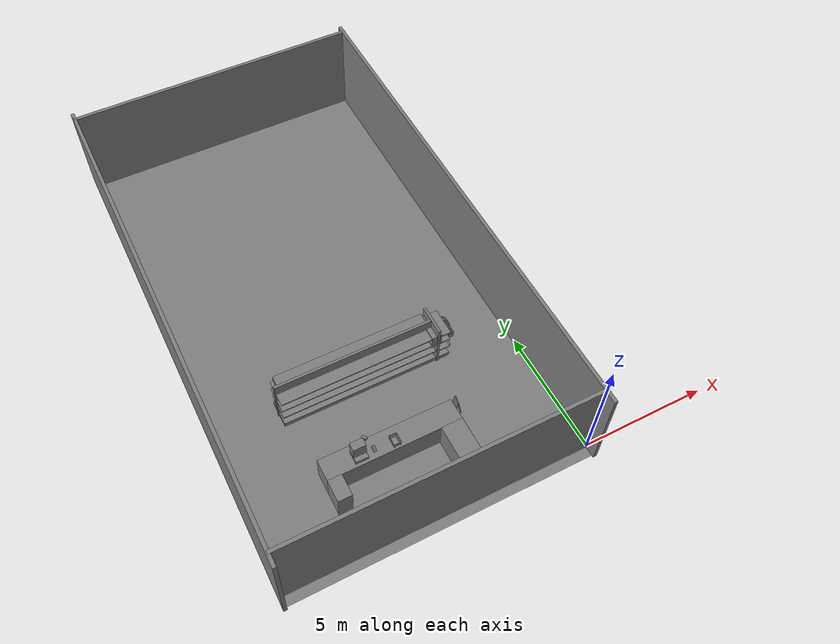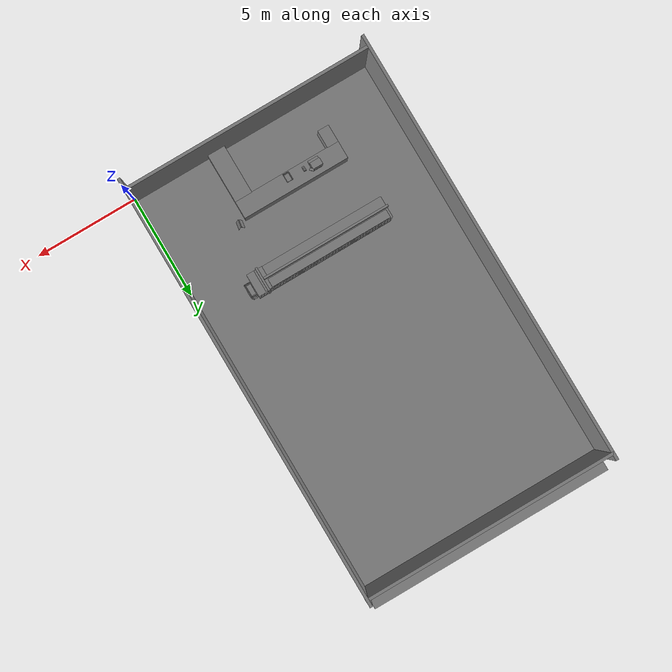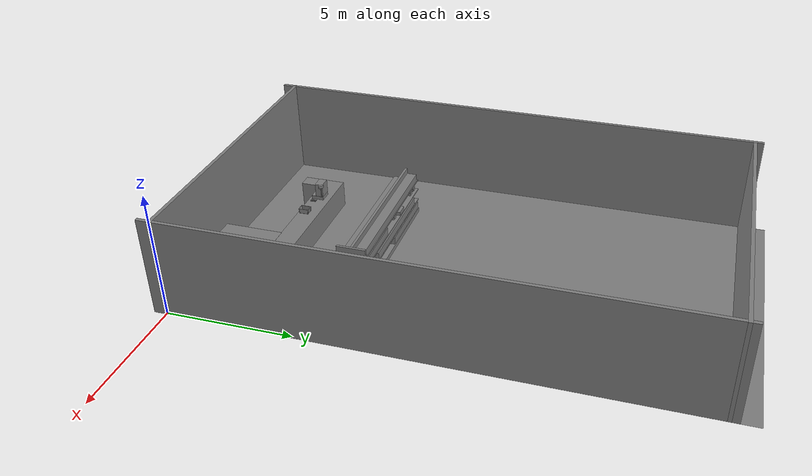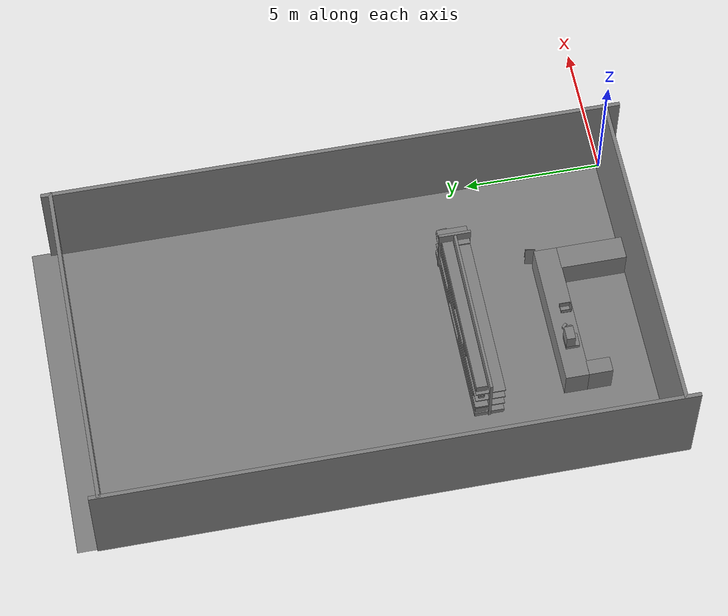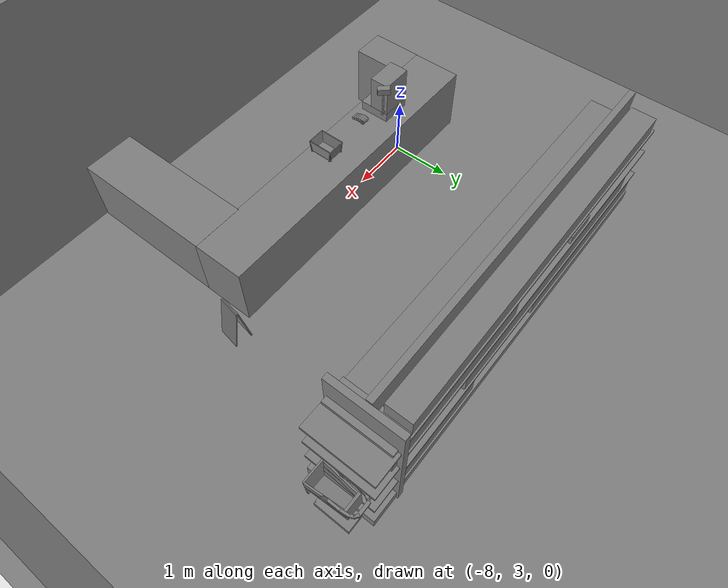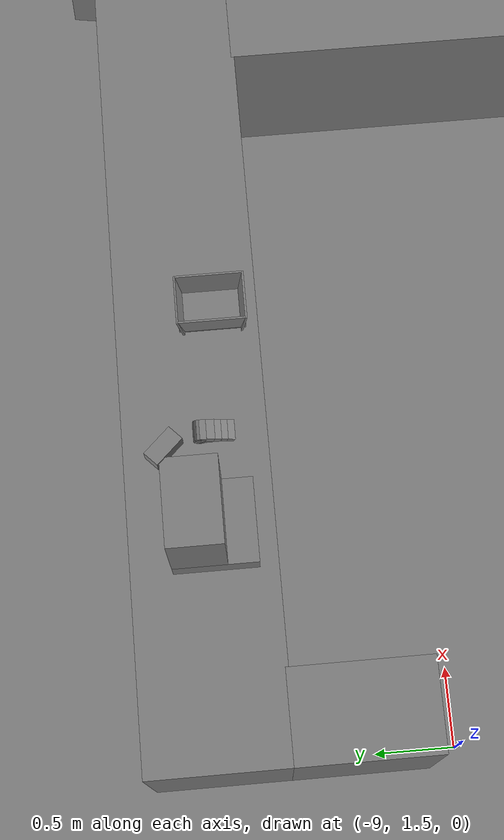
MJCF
<mujoco>
    <option gravity="0.000000000 0.000000000 -9.810000420" timestep="0.0166666" integrator="implicitfast" density="1.225" viscosity="1.8000001e-05" noslip_iterations="10" iterations="100" sdf_iterations="50">
        <flag multiccd="disable"/>
    </option>
    <size memory="1000M"/>
    <compiler coordinate="local"/>
    <worldbody>
        <light cutoff="30" pos="0 1 1" dir="0 -1 -2"/>
        <light cutoff="30" pos="0 -1 1" dir="0 1 -2"/>
        <body pos="-2.436573029 6.404376507 0.137849092" euler="0.000000000 0.000000000 0.000000000" name="openloong_gripper_2f85_fix_base_usda_shoppingtrolley_01">
            <geom contype="1" conaffinity="1" density="1000" type="box" material="" rgba="0.500000000 0.500000000 0.500000000 1.000000000" solimp="0.899999976 0.949999988 0.001000000" friction="1.000000000 0.005000000 0.000100000" solref="0.020000000 1.000000000" margin="0" condim="3" group="0" pos="-0.107458733 0.238907143 0.911498845" quat="0.634576976 0.622505128 -0.330067992 -0.317575932" size="0.017999999 0.022499999 0.035999998" name="openloong_gripper_2f85_fix_base_usda_geom_423EAF29_AF02_4C4E_9E43_1FCD7D4A9CFB"/>
            <geom contype="1" conaffinity="1" density="1000" type="box" material="" rgba="0.500000000 0.500000000 0.500000000 1.000000000" solimp="0.899999976 0.949999988 0.001000000" friction="1.000000000 0.005000000 0.000100000" solref="0.020000000 1.000000000" margin="0" condim="3" group="0" pos="-0.126757339 -0.182533979 0.598989725" quat="0.996607184 0.055331606 -0.059003651 -0.015205891" size="0.013499999 0.287999988 0.053999998" name="openloong_gripper_2f85_fix_base_usda_geom_B4EAC20F_DB15_4A72_BDBF_9DAF228B004E"/>
            <geom contype="1" conaffinity="1" density="1000" type="box" material="" rgba="0.500000000 0.500000000 0.500000000 1.000000000" solimp="0.899999976 0.949999988 0.001000000" friction="1.000000000 0.005000000 0.000100000" solref="0.020000000 1.000000000" margin="0" condim="3" group="0" pos="-0.005004787 0.248085022 0.912686050" quat="1.000000000 0.000000000 0.000000000 0.000000000" size="0.107999995 0.022499999 0.022499999" name="openloong_gripper_2f85_fix_base_usda_geom_37D114A0_A936_448D_A468_E52A1C9BD7E3"/>
            <geom contype="1" conaffinity="1" density="1000" type="box" material="" rgba="0.500000000 0.500000000 0.500000000 1.000000000" solimp="0.899999976 0.949999988 0.001000000" friction="1.000000000 0.005000000 0.000100000" solref="0.020000000 1.000000000" margin="0" condim="3" group="0" pos="-0.169898406 -0.043119621 0.915120542" quat="0.687021017 0.726584017 -0.005590606 -0.006832919" size="0.017999999 0.022499999 0.089999996" name="openloong_gripper_2f85_fix_base_usda_geom_4B50ACD7_76AA_4406_8D49_E3D22B6F288C"/>
            <geom contype="1" conaffinity="1" density="1000" type="box" material="" rgba="0.500000000 0.500000000 0.500000000 1.000000000" solimp="0.899999976 0.949999988 0.001000000" friction="1.000000000 0.005000000 0.000100000" solref="0.020000000 1.000000000" margin="0" condim="3" group="0" pos="0.148195267 -0.199506566 0.782808602" quat="0.998808920 0.017156634 0.026950166 0.036880098" size="0.013499999 0.305999994 0.063000001" name="openloong_gripper_2f85_fix_base_usda_geom_87B827C7_53CB_41EA_9878_23F522AE9876"/>
            <geom contype="1" conaffinity="1" density="1000" type="box" material="" rgba="0.500000000 0.500000000 0.500000000 1.000000000" solimp="0.899999976 0.949999988 0.001000000" friction="1.000000000 0.005000000 0.000100000" solref="0.020000000 1.000000000" margin="0" condim="3" group="0" pos="-0.142927840 -0.199506134 0.784674108" quat="0.998421252 0.016904408 -0.027109101 -0.046199299" size="0.013499999 0.305999994 0.063000001" name="openloong_gripper_2f85_fix_base_usda_geom_F2DE28D9_C288_4B5B_9926_6AB860886742"/>
            <geom contype="1" conaffinity="1" density="1000" type="box" material="" rgba="0.500000000 0.500000000 0.500000000 1.000000000" solimp="0.899999976 0.949999988 0.001000000" friction="1.000000000 0.005000000 0.000100000" solref="0.020000000 1.000000000" margin="0" condim="3" group="0" pos="-0.000004721 -0.174527690 0.560063601" quat="0.996704638 0.081116498 -0.000000004 0.000000000" size="0.126000002 0.287999988 0.009000000" name="openloong_gripper_2f85_fix_base_usda_geom_D4205C36_EA2B_423D_A9E0_DF7B5FFE14DF"/>
            <geom contype="1" conaffinity="1" density="1000" type="box" material="" rgba="0.500000000 0.500000000 0.500000000 1.000000000" solimp="0.899999976 0.949999988 0.001000000" friction="1.000000000 0.005000000 0.000100000" solref="0.020000000 1.000000000" margin="0" condim="3" group="0" pos="-0.160832763 0.103427693 0.910528183" quat="0.711469591 0.699786782 -0.048386075 -0.042050660" size="0.017999999 0.022499999 0.071999997" name="openloong_gripper_2f85_fix_base_usda_geom_4E252498_739C_431B_88D9_CE8D43E214AE"/>
            <geom contype="1" conaffinity="1" density="1000" type="box" material="" rgba="0.500000000 0.500000000 0.500000000 1.000000000" solimp="0.899999976 0.949999988 0.001000000" friction="1.000000000 0.005000000 0.000100000" solref="0.020000000 1.000000000" margin="0" condim="3" group="0" pos="-0.169898406 -0.178061336 0.864131629" quat="0.916343808 -0.400392294 -0.000000045 0.000000030" size="0.017999999 0.022499999 0.089999996" name="openloong_gripper_2f85_fix_base_usda_geom_E32CFDD5_AD78_45BD_8D6C_908C9FED829B"/>
            <geom contype="1" conaffinity="1" density="1000" type="box" material="" rgba="0.500000000 0.500000000 0.500000000 1.000000000" solimp="0.899999976 0.949999988 0.001000000" friction="1.000000000 0.005000000 0.000100000" solref="0.020000000 1.000000000" margin="0" condim="3" group="0" pos="-0.000006008 -0.484932661 0.670727849" quat="0.997585475 0.069449045 -0.000000004 -0.000000089" size="0.179999992 0.013499999 0.170999989" name="openloong_gripper_2f85_fix_base_usda_geom_27E66C97_45C7_4142_98A4_F937B9F0566D"/>
            <geom contype="1" conaffinity="1" density="1000" type="box" material="" rgba="0.500000000 0.500000000 0.500000000 1.000000000" solimp="0.899999976 0.949999988 0.001000000" friction="1.000000000 0.005000000 0.000100000" solref="0.020000000 1.000000000" margin="0" condim="3" group="0" pos="0.134013891 0.200098798 0.912192523" quat="0.692574680 -0.680924535 -0.166899428 0.169783980" size="0.017999999 0.022499999 0.035999998" name="openloong_gripper_2f85_fix_base_usda_geom_017F7778_9C2F_402A_A764_CE20292F0F6D"/>
            <geom contype="1" conaffinity="1" density="1000" type="box" material="" rgba="0.500000000 0.500000000 0.500000000 1.000000000" solimp="0.899999976 0.949999988 0.001000000" friction="1.000000000 0.005000000 0.000100000" solref="0.020000000 1.000000000" margin="0" condim="3" group="0" pos="0.141839072 -0.191051379 0.702451229" quat="0.997147262 0.056065105 0.045779929 0.021407485" size="0.013499999 0.287999988 0.053999998" name="openloong_gripper_2f85_fix_base_usda_geom_7D4F9943_8A30_4DDF_B1E9_BF715048C069"/>
            <geom contype="1" conaffinity="1" density="1000" type="box" material="" rgba="0.500000000 0.500000000 0.500000000 1.000000000" solimp="0.899999976 0.949999988 0.001000000" friction="1.000000000 0.005000000 0.000100000" solref="0.020000000 1.000000000" margin="0" condim="3" group="0" pos="0.169898629 -0.178061336 0.864131629" quat="0.916343808 -0.400392294 -0.000000045 0.000000030" size="0.017999999 0.022499999 0.089999996" name="openloong_gripper_2f85_fix_base_usda_geom_D9B8B4D9_B84D_4142_B354_BE7FB02A5D11"/>
            <geom contype="1" conaffinity="1" density="1000" type="box" material="" rgba="0.500000000 0.500000000 0.500000000 1.000000000" solimp="0.899999976 0.949999988 0.001000000" friction="1.000000000 0.005000000 0.000100000" solref="0.020000000 1.000000000" margin="0" condim="3" group="0" pos="-0.000005364 0.100332208 0.734785020" quat="0.999668717 0.025737956 -0.000000010 0.000000000" size="0.135000005 0.019800000 0.152999997" name="openloong_gripper_2f85_fix_base_usda_geom_D1FAABDD_E7DB_430B_B986_354CC9726914"/>
            <geom contype="1" conaffinity="1" density="1000" type="box" material="" rgba="0.500000000 0.500000000 0.500000000 1.000000000" solimp="0.899999976 0.949999988 0.001000000" friction="1.000000000 0.005000000 0.000100000" solref="0.020000000 1.000000000" margin="0" condim="3" group="0" pos="-0.012634277 -0.174527690 -0.088243507" quat="1.000000000 0.000000000 -0.000000004 0.000000000" size="0.135000005 0.287999988 0.044999998" name="openloong_gripper_2f85_fix_base_usda_geom_B8CA73A0_DD95_455B_90DD_0E43F717598B"/>
            <geom contype="1" conaffinity="1" density="1000" type="box" material="" rgba="0.500000000 0.500000000 0.500000000 1.000000000" solimp="0.899999976 0.949999988 0.001000000" friction="1.000000000 0.005000000 0.000100000" solref="0.020000000 1.000000000" margin="0" condim="3" group="0" pos="0.131482959 -0.182533979 0.598989725" quat="0.996607125 0.055331629 0.059003670 0.015205893" size="0.013499999 0.287999988 0.053999998" name="openloong_gripper_2f85_fix_base_usda_geom_C2AA599F_FF8E_4C02_897A_70126C40847D"/>
            <geom contype="1" conaffinity="1" density="1000" type="box" material="" rgba="0.500000000 0.500000000 0.500000000 1.000000000" solimp="0.899999976 0.949999988 0.001000000" friction="1.000000000 0.005000000 0.000100000" solref="0.020000000 1.000000000" margin="0" condim="3" group="0" pos="0.103667587 0.233050480 0.912927270" quat="0.634205043 -0.622199059 -0.324503720 0.324576139" size="0.017999999 0.022499999 0.035999998" name="openloong_gripper_2f85_fix_base_usda_geom_FEF250D0_A95C_43D1_ABBD_FFADBABA83B7"/>
            <geom contype="1" conaffinity="1" density="1000" type="box" material="" rgba="0.500000000 0.500000000 0.500000000 1.000000000" solimp="0.899999976 0.949999988 0.001000000" friction="1.000000000 0.005000000 0.000100000" solref="0.020000000 1.000000000" margin="0" condim="3" group="0" pos="-0.134013891 0.200098798 0.912192523" quat="0.694057047 0.679413557 -0.172947660 -0.163618833" size="0.017999999 0.022499999 0.035999998" name="openloong_gripper_2f85_fix_base_usda_geom_8CB0AD06_B376_4417_9A18_D1B5A94242E6"/>
            <geom contype="1" conaffinity="1" density="1000" type="box" material="" rgba="0.500000000 0.500000000 0.500000000 1.000000000" solimp="0.899999976 0.949999988 0.001000000" friction="1.000000000 0.005000000 0.000100000" solref="0.020000000 1.000000000" margin="0" condim="3" group="0" pos="-0.135714188 -0.191051379 0.694841146" quat="0.997147322 0.056064609 -0.045779683 -0.021407485" size="0.013499999 0.287999988 0.053999998" name="openloong_gripper_2f85_fix_base_usda_geom_DA5E2EEE_93B6_48BC_AB49_5BDD8AE34775"/>
            <geom contype="1" conaffinity="1" density="1000" type="box" material="" rgba="0.500000000 0.500000000 0.500000000 1.000000000" solimp="0.899999976 0.949999988 0.001000000" friction="1.000000000 0.005000000 0.000100000" solref="0.020000000 1.000000000" margin="0" condim="3" group="0" pos="0.169898629 -0.043119621 0.915120542" quat="0.687029123 -0.726576388 -0.006509603 0.005963952" size="0.017999999 0.022499999 0.089999996" name="openloong_gripper_2f85_fix_base_usda_geom_279EE3F4_0B53_4F65_8EC4_625B5736F693"/>
            <geom contype="1" conaffinity="1" density="1000" type="box" material="" rgba="0.500000000 0.500000000 0.500000000 1.000000000" solimp="0.899999976 0.949999988 0.001000000" friction="1.000000000 0.005000000 0.000100000" solref="0.020000000 1.000000000" margin="0" condim="3" group="0" pos="0.160832971 0.103427693 0.910528183" quat="0.711112797 -0.700149298 -0.042821646 0.047705106" size="0.017999999 0.022499999 0.071999997" name="openloong_gripper_2f85_fix_base_usda_geom_B5372FFC_9C71_406B_8DD1_673B7CEEBF9A"/>
            <freejoint name="openloong_gripper_2f85_fix_base_usda_shoppingtrolley_01_joint"/>
            <site size="0.005000000 0.005000000 0.005000000" rgba="0.500000000 0.500000000 0.500000000 1.000000000" pos="0.000000000 0.000000000 0.000000000" quat="1.000000000 0.000000000 0.000000000 0.000000000" group="0" type="sphere" name="openloong_gripper_2f85_fix_base_usda_shoppingtrolley_01"/>
        </body>
        <body pos="-7.168000221 2.823999882 1.227496982" euler="-0.283413887 0.056829713 -0.133293241" name="openloong_gripper_2f85_fix_base_usda_Pos">
            <geom contype="1" conaffinity="1" density="1000" type="box" material="" rgba="0.500000000 0.500000000 0.500000000 1.000000000" solimp="0.899999976 0.949999988 0.001000000" friction="1.000000000 0.005000000 0.000100000" solref="0.020000000 1.000000000" margin="0" condim="3" group="0" pos="-0.002278805 0.074524641 -0.004134178" quat="0.315989256 0.948762834 0.000000000 0.000000000" size="0.059999999 0.013000000 0.035000000" name="openloong_gripper_2f85_fix_base_usda_geom_501A8D55_C8F5_4D7E_83B7_2B9EF511E72B"/>
            <geom contype="1" conaffinity="1" density="1000" type="box" material="" rgba="0.500000000 0.500000000 0.500000000 1.000000000" solimp="0.899999976 0.949999988 0.001000000" friction="1.000000000 0.005000000 0.000100000" solref="0.020000000 1.000000000" margin="0" condim="3" group="0" pos="-0.002278805 0.078031301 0.008128285" quat="0.990447283 -0.137893349 -0.000000000 0.000000000" size="0.059999999 0.010000000 0.035000000" name="openloong_gripper_2f85_fix_base_usda_geom_62E405EC_BEF5_4B12_B6A6_17B6A5BFD0A6"/>
            <geom contype="1" conaffinity="1" density="1000" type="box" material="" rgba="0.500000000 0.500000000 0.500000000 1.000000000" solimp="0.899999976 0.949999988 0.001000000" friction="1.000000000 0.005000000 0.000100000" solref="0.020000000 1.000000000" margin="0" condim="3" group="0" pos="-0.002278805 0.080785275 -0.002596974" quat="0.287325412 -0.957833171 0.000000000 -0.000000000" size="0.059999999 0.013000000 0.035000000" name="openloong_gripper_2f85_fix_base_usda_geom_119A3212_3175_4658_B930_8E97246CE392"/>
            <geom contype="1" conaffinity="1" density="1000" type="box" material="" rgba="0.500000000 0.500000000 0.500000000 1.000000000" solimp="0.899999976 0.949999988 0.001000000" friction="1.000000000 0.005000000 0.000100000" solref="0.020000000 1.000000000" margin="0" condim="3" group="0" pos="-0.002278805 -0.098804474 -0.020147085" quat="0.988851428 0.148906425 0.000000000 -0.000000000" size="0.059999999 0.022000000 0.020000000" name="openloong_gripper_2f85_fix_base_usda_geom_89AB5757_3FE1_4DA2_ACC8_F002D10A6F94"/>
            <geom contype="1" conaffinity="1" density="1000" type="box" material="" rgba="0.500000000 0.500000000 0.500000000 1.000000000" solimp="0.899999976 0.949999988 0.001000000" friction="1.000000000 0.005000000 0.000100000" solref="0.020000000 1.000000000" margin="0" condim="3" group="0" pos="-0.002279282 0.019920349 0.012102842" quat="0.995421529 0.095583312 -0.000000000 0.000000000" size="0.059999999 0.025000000 0.026000001" name="openloong_gripper_2f85_fix_base_usda_geom_D187B731_681E_40B2_B06D_47CDC46D12CD"/>
            <geom contype="1" conaffinity="1" density="1000" type="box" material="" rgba="0.500000000 0.500000000 0.500000000 1.000000000" solimp="0.899999976 0.949999988 0.001000000" friction="1.000000000 0.005000000 0.000100000" solref="0.020000000 1.000000000" margin="0" condim="3" group="0" pos="-0.002279282 0.005734444 -0.014276981" quat="0.999571502 -0.029275293 -0.000000000 0.000000000" size="0.059999999 0.050000001 0.010000000" name="openloong_gripper_2f85_fix_base_usda_geom_37CFD260_4518_4350_B94D_F8F227E53F96"/>
            <geom contype="1" conaffinity="1" density="1000" type="box" material="" rgba="0.500000000 0.500000000 0.500000000 1.000000000" solimp="0.899999976 0.949999988 0.001000000" friction="1.000000000 0.005000000 0.000100000" solref="0.020000000 1.000000000" margin="0" condim="3" group="0" pos="-0.002278805 0.079460382 0.007771969" quat="0.922590315 -0.385781497 -0.000000000 0.000000000" size="0.059999999 0.010000000 0.035000000" name="openloong_gripper_2f85_fix_base_usda_geom_F500E2E8_D27C_481C_853F_882B5799EB1F"/>
            <geom contype="1" conaffinity="1" density="1000" type="box" material="" rgba="0.500000000 0.500000000 0.500000000 1.000000000" solimp="0.899999976 0.949999988 0.001000000" friction="1.000000000 0.005000000 0.000100000" solref="0.020000000 1.000000000" margin="0" condim="3" group="0" pos="-0.002279282 0.081384182 -0.001320124" quat="0.590483606 -0.807049692 0.000000000 0.000000000" size="0.059999999 0.013000000 0.035000000" name="openloong_gripper_2f85_fix_base_usda_geom_06228D52_F8DC_4F6D_931C_72094B99E96D"/>
            <geom contype="1" conaffinity="1" density="1000" type="box" material="" rgba="0.500000000 0.500000000 0.500000000 1.000000000" solimp="0.899999976 0.949999988 0.001000000" friction="1.000000000 0.005000000 0.000100000" solref="0.020000000 1.000000000" margin="0" condim="3" group="0" pos="-0.002278805 -0.059297562 -0.007972836" quat="0.988851428 0.148906425 0.000000000 -0.000000000" size="0.059999999 0.020000000 0.022000000" name="openloong_gripper_2f85_fix_base_usda_geom_697C2E24_2A69_4C8E_BC2E_B5019FC1F031"/>
            <geom contype="1" conaffinity="1" density="1000" type="box" material="" rgba="0.500000000 0.500000000 0.500000000 1.000000000" solimp="0.899999976 0.949999988 0.001000000" friction="1.000000000 0.005000000 0.000100000" solref="0.020000000 1.000000000" margin="0" condim="3" group="0" pos="-0.002278805 0.076618671 -0.004656911" quat="0.004634960 0.999989390 -0.000000000 0.000000000" size="0.059999999 0.013000000 0.035000000" name="openloong_gripper_2f85_fix_base_usda_geom_8E699BF3_8D6D_4099_A286_B1D64C3055C4"/>
            <geom contype="1" conaffinity="1" density="1000" type="box" material="" rgba="0.500000000 0.500000000 0.500000000 1.000000000" solimp="0.899999976 0.949999988 0.001000000" friction="1.000000000 0.005000000 0.000100000" solref="0.020000000 1.000000000" margin="0" condim="3" group="0" pos="-0.002279282 -0.021952629 0.002959967" quat="0.991270185 0.131847635 0.000000000 -0.000000000" size="0.059999999 0.020000000 0.024000000" name="openloong_gripper_2f85_fix_base_usda_geom_29D2BD81_AA49_4FEF_B0EA_87158B84D72F"/>
            <geom contype="1" conaffinity="1" density="1000" type="box" material="" rgba="0.500000000 0.500000000 0.500000000 1.000000000" solimp="0.899999976 0.949999988 0.001000000" friction="1.000000000 0.005000000 0.000100000" solref="0.020000000 1.000000000" margin="0" condim="3" group="0" pos="-0.002278805 0.081418991 0.002587795" quat="0.803492188 -0.595315576 0.000000000 0.000000000" size="0.059999999 0.013000000 0.035000000" name="openloong_gripper_2f85_fix_base_usda_geom_E5E10CE5_26F7_401A_8127_F66B7F7977AA"/>
            <geom contype="1" conaffinity="1" density="1000" type="box" material="" rgba="0.500000000 0.500000000 0.500000000 1.000000000" solimp="0.899999976 0.949999988 0.001000000" friction="1.000000000 0.005000000 0.000100000" solref="0.020000000 1.000000000" margin="0" condim="3" group="0" pos="-0.002278805 0.061115503 0.008545756" quat="0.999325931 0.036714435 -0.000000000 -0.000000000" size="0.059999999 0.020000000 0.035000000" name="openloong_gripper_2f85_fix_base_usda_geom_50FED6A1_2794_4BE8_9EC9_26C72C293B36"/>
            <freejoint name="openloong_gripper_2f85_fix_base_usda_pos_scan"/>
        </body>
        <body pos="-3.510578632 3.403555870 -0.000000100" euler="0.000000000 0.000000000 40.200675964" name="openloong_gripper_2f85_fix_base_usda_PZ">
            <geom contype="1" conaffinity="1" density="1000" type="box" material="" rgba="0.500000000 0.500000000 0.500000000 1.000000000" solimp="0.899999976 0.949999988 0.001000000" friction="1.000000000 0.005000000 0.000100000" solref="0.020000000 1.000000000" margin="0" condim="3" group="0" pos="-0.047453165 0.056484699 0.373715430" quat="0.934750080 0.077914521 0.028795123 0.345459938" size="0.180000007 0.010000000 0.379999995" name="openloong_gripper_2f85_fix_base_usda_geom_AA200D91_34B4_47A0_8BA3_8570A745E3A1"/>
            <geom contype="1" conaffinity="1" density="1000" type="box" material="" rgba="0.500000000 0.500000000 0.500000000 1.000000000" solimp="0.899999976 0.949999988 0.001000000" friction="1.000000000 0.005000000 0.000100000" solref="0.020000000 1.000000000" margin="0" condim="3" group="0" pos="0.047452450 -0.054376602 0.374072611" quat="0.934387863 -0.082143910 -0.030358355 0.345326364" size="0.180000007 0.010000000 0.379999995" name="openloong_gripper_2f85_fix_base_usda_geom_1F074504_00D1_4146_98F5_FDA17775E37B"/>
            <freejoint name="openloong_gripper_2f85_fix_base_usda_PZ"/>
        </body>
        <body pos="-6.332345009 2.779978037 1.034067392" euler="0.000000000 0.000000000 0.000000000" name="openloong_gripper_2f85_fix_base_usda_basket">
            <geom contype="1" conaffinity="1" density="100000" type="box" material="" rgba="0.500000000 0.500000000 0.500000000 1.000000000" solimp="0.899999976 0.949999988 0.001000000" friction="1.000000000 0.899999976 0.000100000" solref="0.020000000 1.000000000" margin="0" condim="3" group="0" pos="-0.039724827 -0.188568115 0.167089701" quat="0.997537494 0.070135131 0.000000000 0.000000000" size="0.150000006 0.006000000 0.108000003" name="openloong_gripper_2f85_fix_base_usda_geom_A04DEB5A_4E33_4F71_AFC3_6B4B861115DC"/>
            <geom contype="1" conaffinity="1" density="100000" type="box" material="" rgba="0.500000000 0.500000000 0.500000000 1.000000000" solimp="0.899999976 0.949999988 0.001000000" friction="1.000000000 0.899999976 0.000100000" solref="0.020000000 1.000000000" margin="0" condim="3" group="0" pos="0.094372749 0.000000000 0.168361664" quat="0.706172049 0.036353335 0.036353379 0.706171215" size="0.200000003 0.006000000 0.108000003" name="openloong_gripper_2f85_fix_base_usda_geom_AF0D5F82_F054_463C_9F48_350538693E37"/>
            <geom contype="1" conaffinity="1" density="100000" type="box" material="" rgba="0.500000000 0.500000000 0.500000000 1.000000000" solimp="0.899999976 0.949999988 0.001000000" friction="1.000000000 0.899999976 0.000100000" solref="0.020000000 1.000000000" margin="0" condim="3" group="0" pos="-0.039724827 0.000000000 0.068126202" quat="1.000000000 0.000000000 0.000000000 0.000000000" size="0.129999995 0.174999997 0.006000000" name="openloong_gripper_2f85_fix_base_usda_geom_D16C0CA8_DE1B_4EE6_BF22_2F0FEB6FB7CB"/>
            <geom contype="1" conaffinity="1" density="100000" type="box" material="" rgba="0.500000000 0.500000000 0.500000000 1.000000000" solimp="0.899999976 0.949999988 0.001000000" friction="1.000000000 0.899999976 0.000100000" solref="0.020000000 1.000000000" margin="0" condim="3" group="0" pos="-0.039724827 0.188377380 0.167089701" quat="0.997489929 -0.070808925 0.000000000 0.000000000" size="0.150000006 0.006000000 0.108000003" name="openloong_gripper_2f85_fix_base_usda_geom_55E31422_3359_49C7_B99A_7473804D67DB"/>
            <geom contype="1" conaffinity="1" density="100000" type="box" material="" rgba="0.500000000 0.500000000 0.500000000 1.000000000" solimp="0.899999976 0.949999988 0.001000000" friction="1.000000000 0.899999976 0.000100000" solref="0.020000000 1.000000000" margin="0" condim="3" group="0" pos="-0.172339439 0.000000000 0.168361664" quat="0.706172407 -0.036353018 -0.036353093 0.706170976" size="0.200000003 0.006000000 0.108000003" name="openloong_gripper_2f85_fix_base_usda_geom_74E55808_0DD6_48D8_B434_834F05B6B1F7"/>
            <freejoint name="openloong_gripper_2f85_fix_base_usda_basket_joint"/>
            <site size="0.005000000 0.005000000 0.005000000" rgba="0.500000000 0.500000000 0.500000000 1.000000000" pos="0.000000000 0.000000000 0.000000000" quat="1.000000000 0.000000000 0.000000000 0.000000000" group="0" type="sphere" name="openloong_gripper_2f85_fix_base_usda_basketsite"/>
        </body>
        <body pos="0.000000000 0.000000000 0.000000000" euler="0.000000000 0.000000000 0.000000000" name=" Static Objects_ Static Objects">
            <geom contype="1" conaffinity="1" density="1000" type="box" material="" rgba="0.500000000 0.500000000 0.500000000 1.000000000" solimp="0.899999976 0.949999988 0.001000000" friction="1.000000000 0.005000000 0.000100000" solref="0.020000000 1.000000000" margin="0" condim="3" group="0" pos="-6.286010742 6.153595448 1.563861728" quat="0.707107067 0.000000000 0.000000000 0.707106471" size="0.529999971 3.134999990 0.025000000" name=" Static Objects_geom_A7558124_F3C9_43AF_92BC_60DD4DF3D75E"/>
            <geom contype="1" conaffinity="1" density="1000" type="box" material="" rgba="0.500000000 0.500000000 0.500000000 1.000000000" solimp="0.899999976 0.949999988 0.001000000" friction="1.000000000 0.005000000 0.000100000" solref="0.020000000 1.000000000" margin="0" condim="3" group="0" pos="-3.101639986 6.150595188 1.018643856" quat="1.000000000 0.000000000 0.000000000 0.000000000" size="0.050000001 0.579999983 1.019999981" name=" Static Objects_geom_CD4AE130_76F8_44D1_BAD4_EFECDEFB64C7"/>
            <geom contype="1" conaffinity="1" density="1000" type="box" material="" rgba="0.500000000 0.500000000 0.500000000 1.000000000" solimp="0.899999976 0.949999988 0.001000000" friction="1.000000000 0.005000000 0.000100000" solref="0.020000000 1.000000000" margin="0" condim="3" group="0" pos="-2.825197220 6.153595448 1.563861728" quat="0.707107067 0.000000000 0.000000000 0.707106471" size="0.550000012 0.239999995 0.025000000" name=" Static Objects_geom_77343ACC_3009_47E8_9455_A52F361FE961"/>
            <geom contype="1" conaffinity="1" density="1000" type="box" material="" rgba="0.500000000 0.500000000 0.500000000 1.000000000" solimp="0.899999976 0.949999988 0.001000000" friction="1.000000000 0.005000000 0.000100000" solref="0.020000000 1.000000000" margin="0" condim="3" group="0" pos="-6.311686516 6.153595448 1.018643856" quat="0.707107067 0.000000000 0.000000000 0.707106471" size="0.050000001 3.150000095 1.019999981" name=" Static Objects_geom_3A9CEC26_494E_4634_B675_2EF8C475D490"/>
            <geom contype="1" conaffinity="1" density="1000" type="box" material="" rgba="0.500000000 0.500000000 0.500000000 1.000000000" solimp="0.899999976 0.949999988 0.001000000" friction="1.000000000 0.005000000 0.000100000" solref="0.020000000 1.000000000" margin="0" condim="3" group="0" pos="-2.825197220 6.153595448 1.115278244" quat="0.707107067 0.000000000 0.000000000 0.707106471" size="0.550000012 0.239999995 0.025000000" name=" Static Objects_geom_251B0C82_6040_4A65_9FAB_0F36163EC328"/>
            <geom contype="1" conaffinity="1" density="1000" type="box" material="" rgba="0.500000000 0.500000000 0.500000000 1.000000000" solimp="0.899999976 0.949999988 0.001000000" friction="1.000000000 0.005000000 0.000100000" solref="0.020000000 1.000000000" margin="0" condim="3" group="0" pos="-6.293097973 6.153595448 1.114443064" quat="0.707107067 0.000000000 0.000000000 0.707106471" size="0.529999971 3.134999990 0.025000000" name=" Static Objects_geom_9E87B7F6_A51C_4610_85F3_A5D2E9815875"/>
            <geom contype="1" conaffinity="1" density="1000" type="box" material="" rgba="0.500000000 0.500000000 0.500000000 1.000000000" solimp="0.899999976 0.949999988 0.001000000" friction="1.000000000 0.005000000 0.000100000" solref="0.020000000 1.000000000" margin="0" condim="3" group="0" pos="-2.825197220 6.153595448 0.629031777" quat="0.707107067 0.000000000 0.000000000 0.707106471" size="0.550000012 0.239999995 0.025000000" name=" Static Objects_geom_69034A5B_BD91_45BB_99AE_FCD7E2B22675"/>
            <geom contype="1" conaffinity="1" density="1000" type="box" material="" rgba="0.500000000 0.500000000 0.500000000 1.000000000" solimp="0.899999976 0.949999988 0.001000000" friction="1.000000000 0.005000000 0.000100000" solref="0.020000000 1.000000000" margin="0" condim="3" group="0" pos="-6.286010742 6.153595448 0.096129179" quat="0.707107067 0.000000000 0.000000000 0.707106471" size="0.529999971 3.134999990 0.098999999" name=" Static Objects_geom_D5E7A773_5BD1_42E4_95D4_E8079F3AAC8A"/>
            <geom contype="1" conaffinity="1" density="1000" type="box" material="" rgba="0.500000000 0.500000000 0.500000000 1.000000000" solimp="0.899999976 0.949999988 0.001000000" friction="1.000000000 0.005000000 0.000100000" solref="0.020000000 1.000000000" margin="0" condim="3" group="0" pos="-2.825197220 6.153595448 0.097434282" quat="0.707107067 0.000000000 0.000000000 0.707106471" size="0.550000012 0.239999995 0.098999999" name=" Static Objects_geom_3621B078_42A7_476E_97CC_FCF204ED5068"/>
            <geom contype="1" conaffinity="1" density="1000" type="box" material="" rgba="0.500000000 0.500000000 0.500000000 1.000000000" solimp="0.899999976 0.949999988 0.001000000" friction="1.000000000 0.005000000 0.000100000" solref="0.020000000 1.000000000" margin="0" condim="3" group="0" pos="-6.286010742 6.153595448 0.629031777" quat="0.707107067 0.000000000 0.000000000 0.707106471" size="0.529999971 3.134999990 0.025000000" name=" Static Objects_geom_787CB902_65C6_4589_960F_A862DBD915A6"/>
            <geom contype="1" conaffinity="1" density="1000" type="box" material="" rgba="0.500000000 0.500000000 0.500000000 1.000000000" solimp="0.899999976 0.949999988 0.001000000" friction="1.000000000 0.005000000 0.000100000" solref="0.020000000 1.000000000" margin="0" condim="3" group="0" pos="-6.000000000 20.159999847 2.000000000" quat="1.000000000 0.000000000 0.000000000 0.000000000" size="6.079999924 0.070000000 2.000000000" name=" Static Objects_geom_B5C598C3_5770_44BA_A828_69B913AEECA0"/>
            <geom contype="1" conaffinity="1" density="1000" type="box" material="" rgba="0.500000000 0.500000000 0.500000000 1.000000000" solimp="0.899999976 0.949999988 0.001000000" friction="1.000000000 0.005000000 0.000100000" solref="0.020000000 1.000000000" margin="0" condim="3" group="0" pos="-6.000000000 0.035000000 2.000000000" quat="1.000000000 0.000000000 0.000000000 0.000000000" size="6.079999924 0.070000000 2.000000000" name=" Static Objects_geom_95C212AB_97E0_4E3C_B639_2F064763A7A6"/>
            <geom contype="1" conaffinity="1" density="1000" type="box" material="" rgba="0.500000000 0.500000000 0.500000000 1.000000000" solimp="0.899999976 0.949999988 0.001000000" friction="1.000000000 0.005000000 0.000100000" solref="0.020000000 1.000000000" margin="0" condim="3" group="0" pos="0.000000000 10.000000000 2.000000000" quat="1.000000000 0.000000000 0.000000000 0.000000000" size="0.070000000 10.500000000 2.000000000" name=" Static Objects_geom_DA43110E_4C94_4945_B156_594D3F96BEE0"/>
            <geom contype="1" conaffinity="1" density="1000" type="box" material="" rgba="0.500000000 0.500000000 0.500000000 1.000000000" solimp="0.899999976 0.949999988 0.001000000" friction="1.000000000 0.005000000 0.000100000" solref="0.020000000 1.000000000" margin="0" condim="3" group="0" pos="-12.050000191 10.000000000 2.000000000" quat="1.000000000 0.000000000 0.000000000 0.000000000" size="0.070000000 10.500000000 2.000000000" name=" Static Objects_geom_7B713644_9CC7_4241_B42A_0149295DF2AB"/>
            <geom contype="1" conaffinity="1" density="1000" type="plane" material="" rgba="0.500000000 0.500000000 0.500000000 1.000000000" solimp="0.899999976 0.949999988 0.001000000" friction="1.000000000 0.005000000 0.000100000" solref="0.020000000 1.000000000" margin="0" condim="3" group="0" pos="-6.000000000 10.399999619 0.000000000" quat="1.000000000 0.000000000 0.000000000 0.000000000" size="6.050000191 10.800000191 0.010000000" name=" Static Objects_geom_15EA5D90_64EF_4DE3_A020_7E058A506866"/>
            <geom contype="1" conaffinity="1" density="1000" type="box" material="" rgba="0.500000000 0.500000000 0.500000000 1.000000000" solimp="0.899999976 0.949999988 0.001000000" friction="1.000000000 0.005000000 0.000100000" solref="0.020000000 1.000000000" margin="0" condim="3" group="0" pos="-8.830721855 2.096410990 0.549305558" quat="1.000000000 0.000000000 0.000000000 0.000000000" size="0.280000001 0.430000007 0.550000012" name=" Static Objects_geom_E2B203F3_08B5_499F_AF8B_EB477C93A2FC"/>
            <geom contype="1" conaffinity="1" density="1000" type="box" material="" rgba="0.500000000 0.500000000 0.500000000 1.000000000" solimp="0.899999976 0.949999988 0.001000000" friction="1.000000000 0.005000000 0.000100000" solref="0.020000000 1.000000000" margin="0" condim="3" group="0" pos="-6.460197449 2.937205315 0.548931718" quat="1.000000000 0.000000000 0.000000000 0.000000000" size="2.650000095 0.430000007 0.550000012" name=" Static Objects_geom_90A2BCFA_D894_475C_93C8_F9C8F9B965EC"/>
            <geom contype="1" conaffinity="1" density="1000" type="box" material="" rgba="0.500000000 0.500000000 0.500000000 1.000000000" solimp="0.899999976 0.949999988 0.001000000" friction="1.000000000 0.005000000 0.000100000" solref="0.020000000 1.000000000" margin="0" condim="3" group="0" pos="-4.240264893 1.327049494 0.549888909" quat="1.000000000 0.000000000 0.000000000 0.000000000" size="0.430000007 1.200000048 0.550000012" name=" Static Objects_geom_9B63F79C_412D_496F_B746_B6EC513E0E8D"/>
            <geom contype="1" conaffinity="1" density="1000" type="box" material="" rgba="0.500000000 0.500000000 0.500000000 1.000000000" solimp="0.899999976 0.949999988 0.001000000" friction="1.000000000 0.005000000 0.000100000" solref="0.020000000 1.000000000" margin="0" condim="3" group="0" pos="-7.408766270 3.088089943 1.776644945" quat="0.928051054 0.000000000 0.000000000 0.372453064" size="0.050000001 0.100000001 0.050000001" name=" Static Objects_geom_DE557FE6_A058_4871_B19B_1B255787D922"/>
            <geom contype="1" conaffinity="1" density="1000" type="box" material="" rgba="0.500000000 0.500000000 0.500000000 1.000000000" solimp="0.899999976 0.949999988 0.001000000" friction="1.000000000 0.005000000 0.000100000" solref="0.020000000 1.000000000" margin="0" condim="3" group="0" pos="-7.437745571 3.067511320 1.289965630" quat="1.000000000 0.000000000 0.000000000 0.000000000" size="0.029999999 0.020000000 0.020000000" name=" Static Objects_geom_8483E2BC_2004_400D_A34D_E30F0D57A3D8"/>
            <geom contype="1" conaffinity="1" density="1000" type="box" material="" rgba="0.500000000 0.500000000 0.500000000 1.000000000" solimp="0.899999976 0.949999988 0.001000000" friction="1.000000000 0.005000000 0.000100000" solref="0.020000000 1.000000000" margin="0" condim="3" group="0" pos="-7.719123363 2.867671013 1.173410416" quat="1.000000000 0.000000000 0.000000000 0.000000000" size="0.250000000 0.250000000 0.079999998" name=" Static Objects_geom_6BAA7E6E_7E86_4FA9_ADF0_BE4F78D273AF"/>
            <geom contype="1" conaffinity="1" density="1000" type="box" material="" rgba="0.500000000 0.500000000 0.500000000 1.000000000" solimp="0.899999976 0.949999988 0.001000000" friction="1.000000000 0.005000000 0.000100000" solref="0.020000000 1.000000000" margin="0" condim="3" group="0" pos="-7.719123363 2.958004713 1.530241251" quat="1.000000000 0.000000000 0.000000000 0.000000000" size="0.250000000 0.159999996 0.280000001" name=" Static Objects_geom_E0555112_DF92_4BEB_BEB4_EC642C6F1FE5"/>
            <geom contype="1" conaffinity="1" density="1000" type="cylinder" material="" rgba="0.500000000 0.500000000 0.500000000 1.000000000" solimp="0.899999976 0.949999988 0.001000000" friction="1.000000000 0.005000000 0.000100000" solref="0.020000000 1.000000000" margin="0" condim="3" group="0" pos="-7.427312374 3.069516420 1.502544641" quat="0.928051054 0.000000000 0.000000000 0.372453064" size="0.015000000 0.230000004 0.100000001" name=" Static Objects_geom_64EC457A_4786_4783_84BD_1D9E417F0E7D"/>
            <geom contype="1" conaffinity="1" density="1000" type="box" material="" rgba="0.500000000 0.500000000 0.500000000 1.000000000" solimp="0.899999976 0.949999988 0.001000000" friction="1.000000000 0.005000000 0.000100000" solref="0.020000000 1.000000000" margin="0" condim="3" group="0" pos="-9.058088303 6.434794426 1.209077358" quat="1.000000000 0.000000000 0.000000000 0.000000000" size="0.250000000 0.100000001 0.070000000" name=" Static Objects_geom_8A683219_32A1_49FF_B442_B2F5A121ABEA"/>
            <geom contype="1" conaffinity="1" density="1000" type="box" material="" rgba="0.500000000 0.500000000 0.500000000 1.000000000" solimp="0.899999976 0.949999988 0.001000000" friction="1.000000000 0.005000000 0.000100000" solref="0.020000000 1.000000000" margin="0" condim="3" group="0" pos="-5.611940861 6.318420410 0.350975692" quat="1.000000000 0.000000000 0.000000000 0.000000000" size="0.699999988 0.100000001 0.150000006" name=" Static Objects_geom_132B2034_8D27_4B71_9534_A9CFAC2F7831"/>
            <geom contype="1" conaffinity="1" density="1000" type="box" material="" rgba="0.500000000 0.500000000 0.500000000 1.000000000" solimp="0.899999976 0.949999988 0.001000000" friction="1.000000000 0.005000000 0.000100000" solref="0.020000000 1.000000000" margin="0" condim="3" group="0" pos="-9.237723351 6.464855671 1.209077358" quat="1.000000000 0.000000000 0.000000000 0.000000000" size="0.100000001 0.100000001 0.070000000" name=" Static Objects_geom_63DADC08_92F5_4E42_A686_EB47C874D95C"/>
            <geom contype="1" conaffinity="1" density="1000" type="box" material="" rgba="0.500000000 0.500000000 0.500000000 1.000000000" solimp="0.899999976 0.949999988 0.001000000" friction="1.000000000 0.005000000 0.000100000" solref="0.020000000 1.000000000" margin="0" condim="3" group="0" pos="-6.300771236 6.459744930 1.744376063" quat="1.000000000 0.000000000 0.000000000 0.000000000" size="3.000000000 0.200000003 0.150000006" name=" Static Objects_geom_5AC43C72_D002_49EE_8359_912568414505"/>
            <geom contype="1" conaffinity="1" density="1000" type="box" material="" rgba="0.500000000 0.500000000 0.500000000 1.000000000" solimp="0.899999976 0.949999988 0.001000000" friction="1.000000000 0.005000000 0.000100000" solref="0.020000000 1.000000000" margin="0" condim="3" group="0" pos="-7.373087406 6.458900928 1.214329123" quat="1.000000000 0.000000000 0.000000000 0.000000000" size="0.250000000 0.200000003 0.075000003" name=" Static Objects_geom_C497A0EC_F769_45F1_821C_5F7C96CA2EF0"/>
            <geom contype="1" conaffinity="1" density="1000" type="box" material="" rgba="0.500000000 0.500000000 0.500000000 1.000000000" solimp="0.899999976 0.949999988 0.001000000" friction="1.000000000 0.005000000 0.000100000" solref="0.020000000 1.000000000" margin="0" condim="3" group="0" pos="-4.035642624 6.459744930 0.352518857" quat="1.000000000 0.000000000 0.000000000 0.000000000" size="0.800000012 0.200000003 0.150000006" name=" Static Objects_geom_D96431D3_C46F_48F0_B789_D8440EA3BFA5"/>
            <geom contype="1" conaffinity="1" density="1000" type="box" material="" rgba="0.500000000 0.500000000 0.500000000 1.000000000" solimp="0.899999976 0.949999988 0.001000000" friction="1.000000000 0.005000000 0.000100000" solref="0.020000000 1.000000000" margin="0" condim="3" group="0" pos="-3.907610416 6.318625927 0.800981164" quat="1.000000000 0.000000000 0.000000000 0.000000000" size="0.500000000 0.100000001 0.150000006" name=" Static Objects_geom_B91A090C_21D6_42F3_AC42_C2E0BF3EE202"/>
            <geom contype="1" conaffinity="1" density="1000" type="box" material="" rgba="0.500000000 0.500000000 0.500000000 1.000000000" solimp="0.899999976 0.949999988 0.001000000" friction="1.000000000 0.005000000 0.000100000" solref="0.020000000 1.000000000" margin="0" condim="3" group="0" pos="-6.098561764 6.327973843 1.292199373" quat="1.000000000 0.000000000 0.000000000 0.000000000" size="0.500000000 0.100000001 0.150000006" name=" Static Objects_geom_4B6918F2_B1D1_4C47_9061_F021FF5E58F3"/>
            <geom contype="1" conaffinity="1" density="1000" type="box" material="" rgba="0.500000000 0.500000000 0.500000000 1.000000000" solimp="0.899999976 0.949999988 0.001000000" friction="1.000000000 0.005000000 0.000100000" solref="0.020000000 1.000000000" margin="0" condim="3" group="0" pos="-7.886891365 6.459744930 0.352518857" quat="1.000000000 0.000000000 0.000000000 0.000000000" size="1.500000000 0.200000003 0.150000006" name=" Static Objects_geom_752F9AB4_EA2D_48CA_A77C_122E19B1FF51"/>
            <geom contype="1" conaffinity="1" density="1000" type="box" material="" rgba="0.500000000 0.500000000 0.500000000 1.000000000" solimp="0.899999976 0.949999988 0.001000000" friction="1.000000000 0.005000000 0.000100000" solref="0.020000000 1.000000000" margin="0" condim="3" group="0" pos="-6.824534416 6.447464466 1.212718010" quat="1.000000000 0.000000000 0.000000000 0.000000000" size="0.100000001 0.100000001 0.075000003" name=" Static Objects_geom_4037AE8E_800D_482D_9D77_1612BFAADBCD"/>
            <geom contype="1" conaffinity="1" density="1000" type="box" material="" rgba="0.500000000 0.500000000 0.500000000 1.000000000" solimp="0.899999976 0.949999988 0.001000000" friction="1.000000000 0.005000000 0.000100000" solref="0.020000000 1.000000000" margin="0" condim="3" group="0" pos="-4.407354832 6.459744930 1.292199373" quat="1.000000000 0.000000000 0.000000000 0.000000000" size="1.240000010 0.200000003 0.150000006" name=" Static Objects_geom_7086C059_2FFD_4529_8E1D_C9841F4B905B"/>
            <geom contype="1" conaffinity="1" density="1000" type="box" material="" rgba="0.500000000 0.500000000 0.500000000 1.000000000" solimp="0.899999976 0.949999988 0.001000000" friction="1.000000000 0.005000000 0.000100000" solref="0.020000000 1.000000000" margin="0" condim="3" group="0" pos="-6.751636982 6.459744930 0.800981164" quat="1.000000000 0.000000000 0.000000000 0.000000000" size="2.200000048 0.200000003 0.150000006" name=" Static Objects_geom_614AE499_FF75_401D_966E_FFD6912510C8"/>
            <geom contype="1" conaffinity="1" density="1000" type="box" material="" rgba="0.500000000 0.500000000 0.500000000 1.000000000" solimp="0.899999976 0.949999988 0.001000000" friction="1.000000000 0.005000000 0.000100000" solref="0.020000000 1.000000000" margin="0" condim="3" group="0" pos="-6.924745083 6.362090111 1.214329123" quat="1.000000000 0.000000000 0.000000000 0.000000000" size="0.200000003 0.100000001 0.075000003" name=" Static Objects_geom_FAC2A8EF_CA1E_4F2D_A51E_CD4412674A53"/>
            <geom contype="1" conaffinity="1" density="1000" type="box" material="" rgba="0.500000000 0.500000000 0.500000000 1.000000000" solimp="0.899999976 0.949999988 0.001000000" friction="1.000000000 0.005000000 0.000100000" solref="0.020000000 1.000000000" margin="0" condim="3" group="0" pos="-8.844120979 6.464855671 1.209077358" quat="1.000000000 0.000000000 0.000000000 0.000000000" size="0.100000001 0.100000001 0.070000000" name=" Static Objects_geom_420D0460_2810_4BB3_B4B1_62A0080ACAA2"/>
            <geom contype="1" conaffinity="1" density="1000" type="box" material="" rgba="0.500000000 0.500000000 0.500000000 1.000000000" solimp="0.899999976 0.949999988 0.001000000" friction="1.000000000 0.005000000 0.000100000" solref="0.020000000 1.000000000" margin="0" condim="3" group="0" pos="-3.157672644 6.136868477 1.348373055" quat="1.000000000 0.000000000 0.000000000 0.000000000" size="0.200000003 0.519999981 0.300000012" name=" Static Objects_geom_C662E232_7397_4F23_A070_940117389683"/>
        </body>
        <body pos="0.000000000 0.000000000 0.000000000" euler="0.000000000 0.000000000 0.000000000" name="Interactive Objects_Interactive Objects"/>
        <body pos="-2.162922621 6.180304527 -0.123990871" euler="0.000000000 0.000000000 180.000000000" mocap="true" name="openloong_gripper_2f85_fix_base_usda_leftHandMocap"/>
        <body pos="-2.162922621 6.180304527 -0.123990871" euler="0.000000000 0.000000000 180.000000000" mocap="true" name="openloong_gripper_2f85_fix_base_usda_rightHandMocap"/>
        <body pos="-2.162922621 6.180304527 1.076009154" euler="0.000000000 0.000000000 180.000000000" name="openloong_gripper_2f85_fix_base_usda_base_link">
            <geom contype="1" conaffinity="1" density="1000" type="mesh" material="" rgba="0.783999979 0.783999979 0.783999979 1.000000000" solimp="0.899999976 0.949999988 0.001000000" friction="1.000000000 0.005000000 0.000100000" solref="0.020000000 1.000000000" margin="0" condim="3" group="3" mesh="base_link" pos="0.000000000 0.000000000 0.000000000" quat="1.000000000 0.000000000 0.000000000 0.000000000" size="1.000000000 1.000000000 1.000000000" name="openloong_gripper_2f85_fix_base_usda__geom_7_99427212_AC6E_42EF_B7C6_BDA640B73170"/>
            <site size="0.005000000 0.005000000 0.005000000" rgba="0.500000000 0.500000000 0.500000000 1.000000000" pos="0.000000000 0.000000000 0.000000000" quat="1.000000000 0.000000000 0.000000000 0.000000000" group="0" type="sphere" name="openloong_gripper_2f85_fix_base_usda_imu"/>
            <inertial mass="22.447001" pos="-0.005664100 -0.001336700 0.238289997" diaginertia="0.374352545 0.277180195 0.220617250" quat="0.999247074 0.035235517 -0.015086859 0.006023135"/>
            <body pos="0.000000000 0.000000000 0.300000072" euler="0.000000000 0.000000000 0.000000000" name="openloong_gripper_2f85_fix_base_usda_dummy_body">
                <geom contype="1" conaffinity="1" density="1000" type="sphere" material="" rgba="0.783999979 0.783999979 0.783999979 1.000000000" solimp="0.899999976 0.949999988 0.001000000" friction="1.000000000 0.005000000 0.000100000" solref="0.020000000 1.000000000" margin="0" condim="3" group="3" pos="0.000000000 0.000000000 0.000000000" quat="1.000000000 0.000000000 0.000000000 0.000000000" size="0.010000000 0.000000000 0.000000000" name="openloong_gripper_2f85_fix_base_usda__geom_8_46FDD961_0C68_4FEE_BE59_1ABFE43DF4F5"/>
                <joint armature="0.0099999998" stiffness="0" damping="0.1" axis="0.000000 0.000000 1.000000" type="hinge" name="openloong_gripper_2f85_fix_base_usda_dummy_joint"/>
                <site size="0.010000000 0.005000000 0.005000000" rgba="0.500000000 0.500000000 0.500000000 1.000000000" pos="0.000000000 0.000000000 0.000000000" quat="1.000000000 0.000000000 0.000000000 0.000000000" group="3" type="sphere" name="openloong_gripper_2f85_fix_base_usda_dummy_site"/>
            </body>
            <body pos="0.009000063 0.000000000 0.406399965" euler="0.000000000 0.000000000 0.000000000" name="openloong_gripper_2f85_fix_base_usda_Link_head_yaw">
                <geom contype="1" conaffinity="1" density="1000" type="mesh" material="" rgba="0.783999979 0.783999979 0.783999979 1.000000000" solimp="0.899999976 0.949999988 0.001000000" friction="1.000000000 0.005000000 0.000100000" solref="0.020000000 1.000000000" margin="0" condim="3" group="3" mesh="Link_head_yaw" pos="0.000000000 0.000000000 0.000000000" quat="1.000000000 0.000000000 0.000000000 0.000000000" size="1.000000000 1.000000000 1.000000000" name="openloong_gripper_2f85_fix_base_usda__geom_10_A36D028F_EA81_46E6_BD52_30A7EE90010D"/>
                <inertial mass="0.84249002" pos="0.000000000 -0.002081400 0.044801001" diaginertia="0.000700588 0.000629000 0.000553812" quat="0.706933022 -0.015675601 0.015677100 0.706933022"/>
                <body pos="0.000000000 -0.034599781 0.048499942" euler="0.000000000 0.000000000 0.000000000" name="openloong_gripper_2f85_fix_base_usda_Link_head_pitch">
                    <geom contype="1" conaffinity="1" density="1000" type="mesh" material="" rgba="0.783999979 0.783999979 0.783999979 1.000000000" solimp="0.899999976 0.949999988 0.001000000" friction="1.000000000 0.005000000 0.000100000" solref="0.020000000 1.000000000" margin="0" condim="3" group="3" mesh="Link_head_pitch" pos="0.000000000 0.000000000 0.000000000" quat="1.000000000 0.000000000 0.000000000 0.000000000" size="1.000000000 1.000000000 1.000000000" name="openloong_gripper_2f85_fix_base_usda__geom_12_44E38D50_9587_4A8B_B8CC_329A55039313"/>
                    <inertial mass="1.3943" pos="0.020569000 0.033004001 0.125000000" diaginertia="0.006381400 0.006289940 0.004481460" quat="0.973390222 0.008406822 0.228157058 0.019624906"/>
                    <body pos="0.000000000 0.030000210 0.000000000" euler="0.000000000 0.000000000 0.000000000" name="openloong_gripper_2f85_fix_base_usda_neck_center_body">
                        <site size="0.010000000 0.005000000 0.005000000" rgba="0.500000000 0.500000000 0.500000000 1.000000000" pos="0.000000000 0.000000000 0.000000000" quat="1.000000000 0.000000000 0.000000000 0.000000000" group="3" type="sphere" name="openloong_gripper_2f85_fix_base_usda_neck_center_site"/>
                        <body pos="0.019999981 0.000000000 0.149999976" euler="-0.000002229 39.998176575 -90.000205994" name="openloong_gripper_2f85_fix_base_usda_camera_head">
                            <site size="0.010000000 0.005000000 0.005000000" rgba="0.500000000 0.500000000 0.500000000 1.000000000" pos="0.000000000 0.000000000 0.000000000" quat="1.000000000 0.000000000 0.000000000 0.000000000" group="3" type="sphere" name="openloong_gripper_2f85_fix_base_usda_camera_head_site"/>
                        </body>
                    </body>
                </body>
            </body>
            <body pos="0.003999949 -0.161600113 0.392199993" euler="0.000000000 0.000000000 0.000000000" name="openloong_gripper_2f85_fix_base_usda_Link_arm_r_01">
                <geom contype="1" conaffinity="1" density="1000" type="mesh" material="" rgba="0.783999979 0.783999979 0.783999979 1.000000000" solimp="0.899999976 0.949999988 0.001000000" friction="1.000000000 0.005000000 0.000100000" solref="0.020000000 1.000000000" margin="0" condim="3" group="3" mesh="Link_arm_r_01" pos="0.000000000 0.000000000 0.000000000" quat="1.000000000 0.000000000 0.000000000 0.000000000" size="1.000000000 1.000000000 1.000000000" name="openloong_gripper_2f85_fix_base_usda__geom_14_6D715725_6910_4BB3_BD27_3A3A201E174F"/>
                <joint armature="0.0099999998" stiffness="0" damping="1" axis="0.000000 -1.000000 0.000000" limited="true" range="-170.000015259 170.000015259" type="hinge" name="openloong_gripper_2f85_fix_base_usda_J_arm_r_01"/>
                <inertial mass="0.75641" pos="0.004494600 -0.038293999 -0.000001874" diaginertia="0.000842990 0.000803050 0.000587120" quat="-0.000163502 0.707098067 0.000812463 0.707115054"/>
                <body pos="-0.042000055 -0.040999889 0.000000000" euler="0.000000000 0.000000000 0.000000000" name="openloong_gripper_2f85_fix_base_usda_Link_arm_r_02">
                    <geom contype="1" conaffinity="1" density="1000" type="mesh" material="" rgba="0.783999979 0.783999979 0.783999979 1.000000000" solimp="0.899999976 0.949999988 0.001000000" friction="1.000000000 0.005000000 0.000100000" solref="0.020000000 1.000000000" margin="0" condim="3" group="3" mesh="Link_arm_r_02" pos="0.000000000 0.000000000 0.000000000" quat="1.000000000 0.000000000 0.000000000 0.000000000" size="1.000000000 1.000000000 1.000000000" name="openloong_gripper_2f85_fix_base_usda__geom_16_E8101BE3_62CC_40D0_B7AA_A2DE79C2CB35"/>
                    <joint armature="0.0099999998" stiffness="0" damping="1" axis="-1.000000 0.000000 0.000000" limited="true" range="-105.000244141 105.000244141" type="hinge" name="openloong_gripper_2f85_fix_base_usda_J_arm_r_02"/>
                    <inertial mass="0.98500001" pos="0.041999999 -0.067430697 0.000000000" diaginertia="0.002262690 0.001730990 0.001154020" quat="0.500000000 0.500000000 -0.500000000 0.500000000"/>
                    <body pos="0.042000055 -0.122600079 0.000000000" euler="0.000000000 0.000000000 0.000000000" name="openloong_gripper_2f85_fix_base_usda_Link_arm_r_03">
                        <geom contype="1" conaffinity="1" density="1000" type="mesh" material="" rgba="0.783999979 0.783999979 0.783999979 1.000000000" solimp="0.899999976 0.949999988 0.001000000" friction="1.000000000 0.005000000 0.000100000" solref="0.020000000 1.000000000" margin="0" condim="3" group="3" mesh="Link_arm_r_03" pos="0.000000000 0.000000000 0.000000000" quat="1.000000000 0.000000000 0.000000000 0.000000000" size="1.000000000 1.000000000 1.000000000" name="openloong_gripper_2f85_fix_base_usda__geom_18_E4CEFA31_F962_44B6_9878_3F90593E7989"/>
                        <joint armature="0.0099999998" stiffness="0" damping="1" axis="0.000000 -1.000000 0.000000" limited="true" range="-170.000015259 170.000015259" type="hinge" name="openloong_gripper_2f85_fix_base_usda_J_arm_r_03"/>
                        <inertial mass="0.95899999" pos="-0.001413580 -0.164663002 0.020757901" diaginertia="0.002101340 0.002064590 0.000754802" quat="0.560480952 0.454391927 -0.443732947 0.531497955"/>
                        <body pos="0.035300016 -0.177400112 0.024000049" euler="0.000000000 0.000000000 0.000000000" name="openloong_gripper_2f85_fix_base_usda_Link_arm_r_04">
                            <geom contype="1" conaffinity="1" density="1000" type="mesh" material="" rgba="0.783999979 0.783999979 0.783999979 1.000000000" solimp="0.899999976 0.949999988 0.001000000" friction="1.000000000 0.005000000 0.000100000" solref="0.020000000 1.000000000" margin="0" condim="3" group="3" mesh="Link_arm_r_04" pos="0.000000000 0.000000000 0.000000000" quat="1.000000000 0.000000000 0.000000000 0.000000000" size="1.000000000 1.000000000 1.000000000" name="openloong_gripper_2f85_fix_base_usda__geom_20_BFD99148_0311_4A25_94FC_2F911D1A25A9"/>
                            <joint armature="0.0099999998" stiffness="0" damping="1" axis="-1.000000 0.000000 0.000000" limited="true" range="0.000000000 170.000015259" type="hinge" name="openloong_gripper_2f85_fix_base_usda_J_arm_r_04"/>
                            <inertial mass="0.60000002" pos="-0.038727000 -0.060766999 -0.021003000" diaginertia="0.001092610 0.000712422 0.000645102" quat="0.327701002 0.632602990 -0.467366993 0.523443997"/>
                            <body pos="-0.035300016 -0.103499889 -0.024000049" euler="0.000000000 0.000000000 0.000000000" name="openloong_gripper_2f85_fix_base_usda_Link_arm_r_05">
                                <geom contype="1" conaffinity="1" density="1000" type="mesh" material="" rgba="0.783999979 0.783999979 0.783999979 1.000000000" solimp="0.899999976 0.949999988 0.001000000" friction="1.000000000 0.005000000 0.000100000" solref="0.020000000 1.000000000" margin="0" condim="3" group="3" mesh="Link_arm_r_05" pos="0.000000000 0.000000000 0.000000000" quat="1.000000000 0.000000000 0.000000000 0.000000000" size="1.000000000 1.000000000 1.000000000" name="openloong_gripper_2f85_fix_base_usda__geom_22_9CB7A85B_9ACF_4A4C_9D5A_5364A3E1045F"/>
                                <joint armature="0.0099999998" stiffness="0" damping="1" axis="0.000000 -1.000000 0.000000" limited="true" range="-170.000015259 170.000015259" type="hinge" name="openloong_gripper_2f85_fix_base_usda_J_arm_r_05"/>
                                <inertial mass="0.68976003" pos="0.000032712 -0.068658002 -0.000111780" diaginertia="0.002522510 0.002411100 0.000448695" quat="0.707660973 0.706543028 -0.002603360 0.002470550"/>
                                <body pos="-0.026499987 -0.196499825 0.000000000" euler="0.000000000 0.000000000 0.000000000" name="openloong_gripper_2f85_fix_base_usda_Link_arm_r_06">
                                    <geom contype="1" conaffinity="1" density="1000" type="mesh" material="" rgba="0.783999979 0.783999979 0.783999979 1.000000000" solimp="0.899999976 0.949999988 0.001000000" friction="1.000000000 0.005000000 0.000100000" solref="0.020000000 1.000000000" margin="0" condim="3" group="3" mesh="Link_arm_r_06" pos="0.000000000 0.000000000 0.000000000" quat="1.000000000 0.000000000 0.000000000 0.000000000" size="1.000000000 1.000000000 1.000000000" name="openloong_gripper_2f85_fix_base_usda__geom_24_BC1C560F_2A4E_4B52_9AB6_6472F32CE723"/>
                                    <joint armature="0.0099999998" stiffness="0" damping="1" axis="1.000000 0.000000 0.000000" limited="true" range="-105.000244141 105.000244141" type="hinge" name="openloong_gripper_2f85_fix_base_usda_J_arm_r_06"/>
                                    <inertial mass="0.28" pos="0.026078001 -0.000000896 0.001663700" diaginertia="0.000156930 0.000145601 0.000104979" quat="0.707080841 0.001851080 0.001883810 0.707127810"/>
                                    <body pos="0.026499987 0.000000000 0.031800032" euler="0.000000000 0.000000000 0.000000000" name="openloong_gripper_2f85_fix_base_usda_Link_arm_r_07">
                                        <geom contype="1" conaffinity="1" density="1000" type="mesh" material="" rgba="0.783999979 0.783999979 0.783999979 1.000000000" solimp="0.899999976 0.949999988 0.001000000" friction="1.000000000 0.005000000 0.000100000" solref="0.020000000 1.000000000" margin="0" condim="3" group="3" mesh="Link_arm_r_07" pos="0.000000000 0.000000000 0.000000000" quat="1.000000000 0.000000000 0.000000000 0.000000000" size="1.000000000 1.000000000 1.000000000" name="openloong_gripper_2f85_fix_base_usda__geom_26_F2D548C3_7BD2_4631_A1F4_12C319959295"/>
                                        <joint armature="0.0099999998" stiffness="0" damping="1" axis="0.000000 0.000000 1.000000" limited="true" range="-60.000133514 60.000133514" type="hinge" name="openloong_gripper_2f85_fix_base_usda_J_arm_r_07"/>
                                        <inertial mass="0.61353999" pos="-0.007859000 -0.158170000 -0.027736001" diaginertia="0.003037610 0.002570910 0.000729379" quat="0.427542925 0.443532884 -0.553093910 0.560867906"/>
                                        <body pos="0.000000000 0.287000179 -0.269999981" euler="150.000350952 0.000000000 0.000000000" name="openloong_gripper_2f85_fix_base_usda_camera_wrist_r">
                                            <site size="0.010000000 0.005000000 0.005000000" rgba="0.500000000 0.500000000 0.500000000 1.000000000" pos="0.000000000 0.000000000 0.000000000" quat="1.000000000 0.000000000 0.000000000 0.000000000" group="3" type="sphere" name="openloong_gripper_2f85_fix_base_usda_camera_wrist_r_site"/>
                                        </body>
                                        <body pos="0.000000000 -0.219999790 -0.032999992" euler="0.000000000 0.000000000 179.999969482" name="openloong_gripper_2f85_fix_base_usda_ee_center_body_r">
                                            <site size="0.010000000 0.005000000 0.005000000" rgba="0.500000000 0.500000000 0.500000000 1.000000000" pos="0.000000000 0.000000000 0.000000000" quat="1.000000000 0.000000000 0.000000000 0.000000000" group="3" type="sphere" name="openloong_gripper_2f85_fix_base_usda_ee_center_site_r"/>
                                        </body>
                                        <body pos="0.000000000 -0.065999985 -0.031000018" euler="89.999984741 0.000000000 180.000000000" name="openloong_gripper_2f85_fix_base_usda_zbr_base_link">
                                            <geom contype="1" conaffinity="1" density="1000" type="mesh" material="" rgba="0.783999979 0.783999979 0.783999979 1.000000000" solimp="0.899999976 0.949999988 0.001000000" friction="1.000000000 0.005000000 0.000100000" solref="0.020000000 1.000000000" margin="0" condim="3" group="3" mesh="base" pos="0.000000000 0.000000000 0.000000000" quat="1.000000000 0.000000000 0.000000000 0.000000000" size="1.000000238 1.000000238 1.000000238" name="openloong_gripper_2f85_fix_base_usda__geom_30_474124CA_08BC_420F_9B9A_682C33DC9EF6"/>
                                            <inertial mass="0.77744102" pos="0.000000000 -0.000027039 0.035467502" diaginertia="0.000260285 0.000225381 0.000152708" quat="0.999998808 -0.001528488 0.000000000 0.000000000"/>
                                            <body pos="-0.030601032 0.004750133 0.065703884" euler="-89.999977112 0.000000000 0.000000000" name="openloong_gripper_2f85_fix_base_usda_r_left_driver">
                                                <geom contype="1" conaffinity="1" density="1000" type="mesh" material="" rgba="0.783999979 0.783999979 0.783999979 1.000000000" solimp="0.899999976 0.949999988 0.001000000" friction="1.000000000 0.005000000 0.000100000" solref="0.020000000 1.000000000" margin="0" condim="3" group="3" mesh="driver" pos="0.030601032 0.054904476 -0.004699946" quat="0.707106709 0.707106590 0.000000000 0.000000000" size="1.000000238 1.000000238 1.000000238" name="openloong_gripper_2f85_fix_base_usda__geom_32_4836DB51_2896_44B5_9B10_A4ED67661A3F"/>
                                                <joint armature="0.0049999999" stiffness="0" damping="0.1" axis="0.000000 0.000000 1.000000" limited="true" range="0.000000000 51.566200256" type="hinge" name="openloong_gripper_2f85_fix_base_usda_r_left_driver_joint"/>
                                                <inertial mass="0.0089956298" pos="0.000000000 0.017754700 0.001073140" diaginertia="0.000001724 0.000001609 0.000000322" quat="0.681301236 0.732003212 0.000000000 0.000000000"/>
                                                <body pos="-0.031425007 0.004532338 -0.010200026" euler="0.000000000 0.000000000 180.000000000" name="openloong_gripper_2f85_fix_base_usda_r_left_coupler">
                                                    <geom contype="1" conaffinity="1" density="1000" type="mesh" material="" rgba="0.783999979 0.783999979 0.783999979 1.000000000" solimp="0.899999976 0.949999988 0.001000000" friction="1.000000000 0.005000000 0.000100000" solref="0.020000000 1.000000000" margin="0" condim="3" group="3" mesh="coupler" pos="-0.062026039 -0.050372135 0.005499960" quat="0.707106709 -0.707106590 0.000000000 0.000000000" size="1.000000238 1.000000238 1.000000238" name="openloong_gripper_2f85_fix_base_usda__geom_34_47319052_744D_4512_ACBA_6458E0C7063E"/>
                                                    <inertial mass="0.0140974" pos="0.000000000 0.003012090 0.023217499" diaginertia="0.000004162 0.000003522 0.000000888" quat="0.705635548 -0.045590367 0.045590367 0.705635548"/>
                                                </body>
                                            </body>
                                            <body pos="-0.012700084 -0.011999848 0.072219387" euler="-89.999977112 0.000000000 0.000000000" name="openloong_gripper_2f85_fix_base_usda_r_left_spring_link">
                                                <geom contype="1" conaffinity="1" density="1000" type="mesh" material="" rgba="0.783999979 0.783999979 0.783999979 1.000000000" solimp="0.899999976 0.949999988 0.001000000" friction="1.000000000 0.005000000 0.000100000" solref="0.020000000 1.000000000" margin="0" condim="3" group="3" mesh="spring_link" pos="0.012700084 0.061419979 0.012050035" quat="0.707106709 0.707106590 0.000000000 0.000000000" size="1.000000238 1.000000238 1.000000238" name="openloong_gripper_2f85_fix_base_usda__geom_36_5C5014B5_4FE7_4BA8_B817_AB1DF5D07677"/>
                                                <joint armature="0.001" stiffness="0.050000001" damping="0.00125" axis="0.000000 0.000000 1.000000" limited="true" range="-17.000000000 51.566200256" type="hinge" name="openloong_gripper_2f85_fix_base_usda_r_left_spring_link_joint"/>
                                                <inertial mass="0.0221642" pos="-0.000000009 0.018162400 0.021265799" diaginertia="0.000008969 0.000006717 0.000002639" quat="0.663403213 -0.244737089 0.244737089 0.663403213"/>
                                                <body pos="-0.038208015 -0.042500507 0.002949954" euler="180.000000000 0.000000000 -0.002179886" name="openloong_gripper_2f85_fix_base_usda_r_left_follower">
                                                    <geom contype="1" conaffinity="1" density="1000" type="mesh" material="" rgba="0.783999979 0.783999979 0.783999979 1.000000000" solimp="0.899999976 0.949999988 0.001000000" friction="1.000000000 0.005000000 0.000100000" solref="0.020000000 1.000000000" margin="0" condim="3" group="3" mesh="follower" pos="0.050907861 -0.103920005 -0.009100081" quat="0.707106709 -0.707106590 0.000000000 -0.000000000" size="1.000000238 1.000000238 1.000000238" name="openloong_gripper_2f85_fix_base_usda__geom_39_E730FCFF_BE9C_4805_94CE_985B07EF380F"/>
                                                    <geom contype="1" conaffinity="1" density="1000" type="mesh" material="" rgba="0.783999979 0.783999979 0.783999979 1.000000000" solimp="0.899999976 0.949999988 0.001000000" friction="1.000000000 0.005000000 0.000100000" solref="0.020000000 1.000000000" margin="0" condim="3" group="3" mesh="tongue" pos="0.050907861 -0.103920005 -0.009100081" quat="0.707106709 -0.707106590 0.000000000 -0.000000000" size="1.000000238 1.000000238 1.000000238" name="openloong_gripper_2f85_fix_base_usda__geom_40_B593B43E_4592_455C_A447_65A81A4AD772"/>
                                                    <joint armature="0.001" stiffness="0" damping="0.1" axis="0.000000 0.000000 1.000000" limited="true" range="-49.999961853 51.566200256" type="hinge" name="openloong_gripper_2f85_fix_base_usda_r_left_follower"/>
                                                    <inertial mass="0.0125222" pos="0.000000000 -0.011046000 0.012478600" diaginertia="0.000002674 0.000002456 0.000000602" quat="0.986436546 0.164143041 0.000000000 0.000000000"/>
                                                    <body pos="-0.037789829 -0.103916191 -0.009100081" euler="-89.999961853 0.000000000 -0.000000000" name="openloong_gripper_2f85_fix_base_usda_r_left_pad">
                                                        <geom contype="1" conaffinity="1" density="1000" type="box" material="" rgba="0.449999988 0.449999988 0.449999988 1.000000000" solimp="0.949999988 0.990000010 0.001000000" friction="0.600000024 0.005000000 0.000100000" solref="0.020000000 1.000000000" margin="0" condim="3" group="3" mass="1e-06" pos="0.043257724 -0.000000119 0.138749629" quat="0.999999821 0.000000000 0.000000000 0.000000000" size="0.002000001 0.011000003 0.009375002" name="openloong_gripper_2f85_fix_base_usda_r_left_pad2_2116CE42_430E_4843_8A1B_360F291FD359"/>
                                                        <geom contype="1" conaffinity="1" density="1000" type="box" material="" rgba="0.550000012 0.550000012 0.550000012 1.000000000" solimp="0.949999988 0.990000010 0.001000000" friction="0.699999988 0.005000000 0.000100000" solref="0.020000000 1.000000000" margin="0" condim="3" group="3" mass="1e-06" pos="0.043257724 -0.000000119 0.120000392" quat="0.999999821 0.000000000 0.000000000 0.000000000" size="0.002000001 0.011000003 0.009375002" name="openloong_gripper_2f85_fix_base_usda_r_left_pad1_302707B4_8955_485E_A10D_F3486755B480"/>
                                                    </body>
                                                </body>
                                            </body>
                                            <body pos="0.030601032 -0.004749895 0.065703884" euler="89.999984741 0.000000000 180.000000000" name="openloong_gripper_2f85_fix_base_usda_r_right_driver">
                                                <geom contype="1" conaffinity="1" density="1000" type="mesh" material="" rgba="0.783999979 0.783999979 0.783999979 1.000000000" solimp="0.899999976 0.949999988 0.001000000" friction="1.000000000 0.005000000 0.000100000" solref="0.020000000 1.000000000" margin="0" condim="3" group="3" mesh="driver" pos="0.030601032 0.054904476 -0.004699946" quat="0.707106829 0.707106709 0.000000000 0.000000000" size="1.000000238 1.000000238 1.000000238" name="openloong_gripper_2f85_fix_base_usda__geom_42_5727AFF9_655C_4FF9_890D_83F59E0EBF9D"/>
                                                <joint armature="0.0049999999" stiffness="0" damping="0.1" axis="0.000000 0.000000 1.000000" limited="true" range="0.000000000 51.566200256" type="hinge" name="openloong_gripper_2f85_fix_base_usda_r_right_driver_joint"/>
                                                <inertial mass="0.0089956298" pos="0.000000000 0.017754700 0.001073140" diaginertia="0.000001724 0.000001609 0.000000322" quat="0.681301236 0.732003212 0.000000000 0.000000000"/>
                                                <body pos="-0.031425007 0.004532338 -0.010200026" euler="0.000000000 0.000000000 180.000000000" name="openloong_gripper_2f85_fix_base_usda_r_right_coupler">
                                                    <geom contype="1" conaffinity="1" density="1000" type="mesh" material="" rgba="0.783999979 0.783999979 0.783999979 1.000000000" solimp="0.899999976 0.949999988 0.001000000" friction="1.000000000 0.005000000 0.000100000" solref="0.020000000 1.000000000" margin="0" condim="3" group="3" mesh="coupler" pos="-0.062026039 -0.050372135 0.005499960" quat="0.707106829 -0.707106709 0.000000000 0.000000000" size="1.000000238 1.000000238 1.000000238" name="openloong_gripper_2f85_fix_base_usda__geom_44_5E0718D5_2FAD_4B67_BC09_D1DF60A5A589"/>
                                                    <inertial mass="0.0140974" pos="0.000000000 0.003012090 0.023217499" diaginertia="0.000004162 0.000003522 0.000000888" quat="0.705635548 -0.045590367 0.045590367 0.705635548"/>
                                                </body>
                                            </body>
                                            <body pos="0.012700084 0.012000087 0.072219387" euler="89.999984741 0.000000000 180.000000000" name="openloong_gripper_2f85_fix_base_usda_r_right_spring_link">
                                                <geom contype="1" conaffinity="1" density="1000" type="mesh" material="" rgba="0.783999979 0.783999979 0.783999979 1.000000000" solimp="0.899999976 0.949999988 0.001000000" friction="1.000000000 0.005000000 0.000100000" solref="0.020000000 1.000000000" margin="0" condim="3" group="3" mesh="spring_link" pos="0.012700084 0.061419979 0.012050035" quat="0.707106829 0.707106709 0.000000000 0.000000000" size="1.000000238 1.000000238 1.000000238" name="openloong_gripper_2f85_fix_base_usda__geom_46_25CE6848_0AED_4401_B4BB_77D18CD615E6"/>
                                                <joint armature="0.001" stiffness="0.050000001" damping="0.00125" axis="0.000000 0.000000 1.000000" limited="true" range="-17.000000000 51.566200256" type="hinge" name="openloong_gripper_2f85_fix_base_usda_r_right_spring_link_joint"/>
                                                <inertial mass="0.0221642" pos="-0.000000009 0.018162400 0.021265799" diaginertia="0.000008969 0.000006717 0.000002639" quat="0.663403213 -0.244737089 0.244737089 0.663403213"/>
                                                <body pos="-0.038208015 -0.042500507 0.002949954" euler="180.000000000 0.000000000 0.000000000" name="openloong_gripper_2f85_fix_base_usda_r_right_follower">
                                                    <geom contype="1" conaffinity="1" density="1000" type="mesh" material="" rgba="0.783999979 0.783999979 0.783999979 1.000000000" solimp="0.899999976 0.949999988 0.001000000" friction="1.000000000 0.005000000 0.000100000" solref="0.020000000 1.000000000" margin="0" condim="3" group="3" mesh="follower" pos="0.050907861 -0.103920005 -0.009099962" quat="0.707106829 -0.707106709 0.000000000 0.000000000" size="1.000000238 1.000000238 1.000000238" name="openloong_gripper_2f85_fix_base_usda__geom_50_0E4F2C9C_0F65_4BBF_88C0_990DC3D3F9E5"/>
                                                    <geom contype="1" conaffinity="1" density="1000" type="mesh" material="" rgba="0.783999979 0.783999979 0.783999979 1.000000000" solimp="0.899999976 0.949999988 0.001000000" friction="1.000000000 0.005000000 0.000100000" solref="0.020000000 1.000000000" margin="0" condim="3" group="3" mesh="tongue" pos="0.050907861 -0.103920005 -0.009099962" quat="0.707106829 -0.707106709 0.000000000 0.000000000" size="1.000000238 1.000000238 1.000000238" name="openloong_gripper_2f85_fix_base_usda__geom_49_55845629_FEA3_4341_A84F_2A94D0F91DE6"/>
                                                    <joint armature="0.001" stiffness="0" damping="0.1" axis="0.000000 0.000000 1.000000" limited="true" range="-49.999961853 51.566200256" type="hinge" name="openloong_gripper_2f85_fix_base_usda_r_right_follower_joint"/>
                                                    <inertial mass="0.0125222" pos="0.000000000 -0.011046000 0.012478600" diaginertia="0.000002674 0.000002456 0.000000602" quat="0.986436546 0.164143041 0.000000000 0.000000000"/>
                                                    <body pos="-0.037789829 -0.103916191 -0.009099962" euler="-89.999984741 0.000000000 0.000000000" name="openloong_gripper_2f85_fix_base_usda_r_right_pad">
                                                        <geom contype="1" conaffinity="1" density="1000" type="box" material="" rgba="0.550000012 0.550000012 0.550000012 1.000000000" solimp="0.949999988 0.990000010 0.001000000" friction="0.699999988 0.005000000 0.000100000" solref="0.020000000 1.000000000" margin="0" condim="3" group="3" mass="1e-06" pos="0.043257963 -0.000000596 0.119998962" quat="1.000000000 0.000000000 0.000000000 0.000000000" size="0.002000001 0.011000003 0.009375002" name="openloong_gripper_2f85_fix_base_usda_r_right_pad1_3BF6D4D1_F0D3_4534_8B1E_88D486EB87F9"/>
                                                        <geom contype="1" conaffinity="1" density="1000" type="box" material="" rgba="0.449999988 0.449999988 0.449999988 1.000000000" solimp="0.949999988 0.990000010 0.001000000" friction="0.600000024 0.005000000 0.000100000" solref="0.020000000 1.000000000" margin="0" condim="3" group="3" mass="1e-06" pos="0.043257963 -0.000000596 0.138749152" quat="1.000000000 0.000000000 0.000000000 0.000000000" size="0.002000001 0.011000003 0.009375002" name="openloong_gripper_2f85_fix_base_usda_r_right_pad2_984D8641_73A8_4E56_B64A_4E711305730A"/>
                                                    </body>
                                                </body>
                                            </body>
                                        </body>
                                    </body>
                                </body>
                            </body>
                        </body>
                    </body>
                </body>
            </body>
            <body pos="0.003999949 0.161600113 0.392199993" euler="0.000000000 0.000000000 0.000000000" name="openloong_gripper_2f85_fix_base_usda_Link_arm_l_01">
                <geom contype="1" conaffinity="1" density="1000" type="mesh" material="" rgba="0.783999979 0.783999979 0.783999979 1.000000000" solimp="0.899999976 0.949999988 0.001000000" friction="1.000000000 0.005000000 0.000100000" solref="0.020000000 1.000000000" margin="0" condim="3" group="3" mesh="Link_arm_l_01" pos="0.000000000 0.000000000 0.000000000" quat="1.000000000 0.000000000 0.000000000 0.000000000" size="1.000000000 1.000000000 1.000000000" name="openloong_gripper_2f85_fix_base_usda__geom_52_C862BE5A_8EBE_47F5_957C_3571E6468FB9"/>
                <joint armature="0.0099999998" stiffness="0" damping="1" axis="0.000000 1.000000 0.000000" limited="true" range="-170.000015259 170.000015259" type="hinge" name="openloong_gripper_2f85_fix_base_usda_J_arm_l_01"/>
                <inertial mass="0.75640601" pos="-0.004494650 0.038294200 -0.000001874" diaginertia="0.000842986 0.000803053 0.000587115" quat="-0.000812496 0.707115054 0.000163424 0.707098067"/>
                <body pos="0.042000055 0.040999889 0.000000000" euler="0.000000000 0.000000000 0.000000000" name="openloong_gripper_2f85_fix_base_usda_Link_arm_l_02">
                    <geom contype="1" conaffinity="1" density="1000" type="mesh" material="" rgba="0.783999979 0.783999979 0.783999979 1.000000000" solimp="0.899999976 0.949999988 0.001000000" friction="1.000000000 0.005000000 0.000100000" solref="0.020000000 1.000000000" margin="0" condim="3" group="3" mesh="Link_arm_l_02" pos="0.000000000 0.000000000 0.000000000" quat="1.000000000 0.000000000 0.000000000 0.000000000" size="1.000000000 1.000000000 1.000000000" name="openloong_gripper_2f85_fix_base_usda__geom_54_CC1435FC_3193_40C0_A714_F27C12F92C63"/>
                    <joint armature="0.0099999998" stiffness="0" damping="1" axis="-1.000000 0.000000 0.000000" limited="true" range="-105.000244141 105.000244141" type="hinge" name="openloong_gripper_2f85_fix_base_usda_J_arm_l_02"/>
                    <inertial mass="0.98500001" pos="-0.041999999 0.067430697 0.000000000" diaginertia="0.002262690 0.001730990 0.001154020" quat="0.500000000 0.500000000 -0.500000000 0.500000000"/>
                    <body pos="-0.042000055 0.122600079 0.000000000" euler="0.000000000 0.000000000 0.000000000" name="openloong_gripper_2f85_fix_base_usda_Link_arm_l_03">
                        <geom contype="1" conaffinity="1" density="1000" type="mesh" material="" rgba="0.783999979 0.783999979 0.783999979 1.000000000" solimp="0.899999976 0.949999988 0.001000000" friction="1.000000000 0.005000000 0.000100000" solref="0.020000000 1.000000000" margin="0" condim="3" group="3" mesh="Link_arm_l_03" pos="0.000000000 0.000000000 0.000000000" quat="1.000000000 0.000000000 0.000000000 0.000000000" size="1.000000000 1.000000000 1.000000000" name="openloong_gripper_2f85_fix_base_usda__geom_56_AB5C0CDE_50A2_46AB_8F78_2DA6D9AED057"/>
                        <joint armature="0.0099999998" stiffness="0" damping="1" axis="0.000000 1.000000 0.000000" limited="true" range="-170.000015259 170.000015259" type="hinge" name="openloong_gripper_2f85_fix_base_usda_J_arm_l_03"/>
                        <inertial mass="0.95899999" pos="0.001413580 0.164663002 0.020757901" diaginertia="0.002101340 0.002064590 0.000754802" quat="0.443732947 0.531497955 -0.560480952 0.454391927"/>
                        <body pos="-0.035300016 0.177400112 0.024000049" euler="0.000000000 0.000000000 0.000000000" name="openloong_gripper_2f85_fix_base_usda_Link_arm_l_04">
                            <geom contype="1" conaffinity="1" density="1000" type="mesh" material="" rgba="0.783999979 0.783999979 0.783999979 1.000000000" solimp="0.899999976 0.949999988 0.001000000" friction="1.000000000 0.005000000 0.000100000" solref="0.020000000 1.000000000" margin="0" condim="3" group="3" mesh="Link_arm_l_04" pos="0.000000000 0.000000000 0.000000000" quat="1.000000000 0.000000000 0.000000000 0.000000000" size="1.000000000 1.000000000 1.000000000" name="openloong_gripper_2f85_fix_base_usda__geom_58_B54BC58B_F54F_4E7E_9247_A22A717459CD"/>
                            <joint armature="0.0099999998" stiffness="0" damping="1" axis="1.000000 0.000000 0.000000" limited="true" range="0.000000000 170.000015259" type="hinge" name="openloong_gripper_2f85_fix_base_usda_J_arm_l_04"/>
                            <inertial mass="0.60000002" pos="0.038727000 0.060767200 -0.021003200" diaginertia="0.001092570 0.000712419 0.000645098" quat="0.467370987 0.523440003 -0.327692002 0.632607996"/>
                            <body pos="0.035300016 0.103499889 -0.024000049" euler="0.000000000 0.000000000 0.000000000" name="openloong_gripper_2f85_fix_base_usda_Link_arm_l_05">
                                <geom contype="1" conaffinity="1" density="1000" type="mesh" material="" rgba="0.783999979 0.783999979 0.783999979 1.000000000" solimp="0.899999976 0.949999988 0.001000000" friction="1.000000000 0.005000000 0.000100000" solref="0.020000000 1.000000000" margin="0" condim="3" group="3" mesh="Link_arm_l_05" pos="0.000000000 0.000000000 0.000000000" quat="1.000000000 0.000000000 0.000000000 0.000000000" size="1.000000000 1.000000000 1.000000000" name="openloong_gripper_2f85_fix_base_usda__geom_60_39D5843D_DCE0_4831_A0A5_8D02289B2F27"/>
                                <joint armature="0.0099999998" stiffness="0" damping="1" axis="0.000000 1.000000 0.000000" limited="true" range="-170.000015259 170.000015259" type="hinge" name="openloong_gripper_2f85_fix_base_usda_J_arm_l_05"/>
                                <inertial mass="0.68976003" pos="-0.000032712 0.068658002 -0.000111780" diaginertia="0.002522510 0.002411100 0.000448695" quat="0.706543028 0.707660973 0.002470550 -0.002603360"/>
                                <body pos="0.026499987 0.196499825 0.000000000" euler="0.000000000 0.000000000 0.000000000" name="openloong_gripper_2f85_fix_base_usda_Link_arm_l_06">
                                    <geom contype="1" conaffinity="1" density="1000" type="mesh" material="" rgba="0.783999979 0.783999979 0.783999979 1.000000000" solimp="0.899999976 0.949999988 0.001000000" friction="1.000000000 0.005000000 0.000100000" solref="0.020000000 1.000000000" margin="0" condim="3" group="3" mesh="Link_arm_l_06" pos="0.000000000 0.000000000 0.000000000" quat="1.000000000 0.000000000 0.000000000 0.000000000" size="1.000000000 1.000000000 1.000000000" name="openloong_gripper_2f85_fix_base_usda__geom_62_C9361ACA_FD07_48E4_B565_093D8F3CF636"/>
                                    <joint armature="0.0099999998" stiffness="0" damping="1" axis="-1.000000 0.000000 0.000000" limited="true" range="-105.000244141 105.000244141" type="hinge" name="openloong_gripper_2f85_fix_base_usda_J_arm_l_06"/>
                                    <inertial mass="0.28" pos="-0.026077701 0.000000896 0.001663730" diaginertia="0.000156927 0.000145598 0.000104981" quat="0.707080841 -0.001851280 -0.001884020 0.707127810"/>
                                    <body pos="-0.026499987 0.000000000 0.031800032" euler="0.000000000 0.000000000 0.000000000" name="openloong_gripper_2f85_fix_base_usda_Link_arm_l_07">
                                        <geom contype="1" conaffinity="1" density="1000" type="mesh" material="" rgba="0.783999979 0.783999979 0.783999979 1.000000000" solimp="0.899999976 0.949999988 0.001000000" friction="1.000000000 0.005000000 0.000100000" solref="0.020000000 1.000000000" margin="0" condim="3" group="3" mesh="Link_arm_l_07" pos="0.000000000 0.000000000 0.000000000" quat="1.000000000 0.000000000 0.000000000 0.000000000" size="1.000000000 1.000000000 1.000000000" name="openloong_gripper_2f85_fix_base_usda__geom_64_018E8E3C_66FB_4CA9_96A9_37FFAF7AAEA7"/>
                                        <joint armature="0.0099999998" stiffness="0" damping="1" axis="0.000000 0.000000 1.000000" limited="true" range="-60.000133514 60.000133514" type="hinge" name="openloong_gripper_2f85_fix_base_usda_J_arm_l_07"/>
                                        <inertial mass="0.61353999" pos="-0.007787200 0.157049999 -0.027733000" diaginertia="0.003037200 0.002570420 0.000729374" quat="0.443562120 0.427539080 -0.560871124 0.553070128"/>
                                        <body pos="0.000000000 -0.287000179 -0.269999981" euler="-150.000350952 -0.000000001 179.976669312" name="openloong_gripper_2f85_fix_base_usda_camera_wrist_l">
                                            <site size="0.010000000 0.005000000 0.005000000" rgba="0.500000000 0.500000000 0.500000000 1.000000000" pos="0.000000000 0.000000000 0.000000000" quat="1.000000000 0.000000000 0.000000000 0.000000000" group="3" type="sphere" name="openloong_gripper_2f85_fix_base_usda_camera_wrist_l_site"/>
                                        </body>
                                        <body pos="0.000000000 0.219999790 -0.032999992" euler="0.000000000 0.000000000 0.000000000" name="openloong_gripper_2f85_fix_base_usda_ee_center_body">
                                            <site size="0.010000000 0.005000000 0.005000000" rgba="0.500000000 0.500000000 0.500000000 1.000000000" pos="0.000000000 0.000000000 0.000000000" quat="1.000000000 0.000000000 0.000000000 0.000000000" group="3" type="sphere" name="openloong_gripper_2f85_fix_base_usda_ee_center_site"/>
                                        </body>
                                        <body pos="0.000000000 0.065999985 -0.031000018" euler="-90.000007629 0.000000000 0.000000000" name="openloong_gripper_2f85_fix_base_usda_zbll_base_link">
                                            <geom contype="1" conaffinity="1" density="1000" type="mesh" material="" rgba="0.783999979 0.783999979 0.783999979 1.000000000" solimp="0.899999976 0.949999988 0.001000000" friction="1.000000000 0.005000000 0.000100000" solref="0.020000000 1.000000000" margin="0" condim="3" group="3" mesh="base" pos="0.000000000 0.000000000 0.000000000" quat="1.000000000 0.000000000 0.000000000 0.000000000" size="1.000000000 1.000000000 1.000000000" name="openloong_gripper_2f85_fix_base_usda__geom_68_87C82D1E_C8D7_4B3C_BB76_3AC7B0F5EBBB"/>
                                            <inertial mass="0.77744102" pos="0.000000000 -0.000027039 0.035467502" diaginertia="0.000260285 0.000225381 0.000152708" quat="0.999998808 -0.001528488 0.000000000 0.000000000"/>
                                            <body pos="-0.030601025 0.004750252 0.065703869" euler="-89.999992371 0.000000000 0.000000000" name="openloong_gripper_2f85_fix_base_usda_l_left_driver">
                                                <geom contype="1" conaffinity="1" density="1000" type="mesh" material="" rgba="0.783999979 0.783999979 0.783999979 1.000000000" solimp="0.899999976 0.949999988 0.001000000" friction="1.000000000 0.005000000 0.000100000" solref="0.020000000 1.000000000" margin="0" condim="3" group="3" mesh="driver" pos="0.030601025 0.054904461 -0.004699945" quat="0.707106829 0.707106709 0.000000000 0.000000000" size="1.000000000 1.000000000 1.000000000" name="openloong_gripper_2f85_fix_base_usda__geom_70_57FE675C_C274_4B0C_8C73_CE329FE86203"/>
                                                <joint armature="0.0049999999" stiffness="0" damping="0.1" axis="0.000000 0.000000 1.000000" limited="true" range="0.000000000 51.566200256" type="hinge" name="openloong_gripper_2f85_fix_base_usda_l_left_driver_joint"/>
                                                <inertial mass="0.0089956298" pos="0.000000000 0.017754700 0.001073140" diaginertia="0.000001724 0.000001609 0.000000322" quat="0.681301236 0.732003212 0.000000000 0.000000000"/>
                                                <body pos="-0.031424999 0.004532337 -0.010200024" euler="0.000000000 0.000000000 180.000000000" name="openloong_gripper_2f85_fix_base_usda_l_left_coupler">
                                                    <geom contype="1" conaffinity="1" density="1000" type="mesh" material="" rgba="0.783999979 0.783999979 0.783999979 1.000000000" solimp="0.899999976 0.949999988 0.001000000" friction="1.000000000 0.005000000 0.000100000" solref="0.020000000 1.000000000" margin="0" condim="3" group="3" mesh="coupler" pos="-0.062026024 -0.050372124 0.005499959" quat="0.707106829 -0.707106709 0.000000000 0.000000000" size="1.000000000 1.000000000 1.000000000" name="openloong_gripper_2f85_fix_base_usda__geom_72_C4915546_201F_4DA5_8BB9_59BFD84FB2B0"/>
                                                    <inertial mass="0.0140974" pos="0.000000000 0.003012090 0.023217499" diaginertia="0.000004162 0.000003522 0.000000888" quat="0.705635548 -0.045590367 0.045590367 0.705635548"/>
                                                </body>
                                            </body>
                                            <body pos="-0.012700081 -0.011999846 0.072219849" euler="-89.999992371 0.000000000 0.000000000" name="openloong_gripper_2f85_fix_base_usda_l_left_spring_link">
                                                <geom contype="1" conaffinity="1" density="1000" type="mesh" material="" rgba="0.783999979 0.783999979 0.783999979 1.000000000" solimp="0.899999976 0.949999988 0.001000000" friction="1.000000000 0.005000000 0.000100000" solref="0.020000000 1.000000000" margin="0" condim="3" group="3" mesh="spring_link" pos="0.012700081 0.061419964 0.012050033" quat="0.707106829 0.707106709 0.000000000 0.000000000" size="1.000000000 1.000000000 1.000000000" name="openloong_gripper_2f85_fix_base_usda__geom_74_371C48E6_724B_419B_8804_D50A1E32691B"/>
                                                <joint armature="0.001" stiffness="0.050000001" damping="0.00125" axis="0.000000 0.000000 1.000000" limited="true" range="-17.000000000 51.566200256" type="hinge" name="openloong_gripper_2f85_fix_base_usda_l_left_spring_link_joint"/>
                                                <inertial mass="0.0221642" pos="-0.000000009 0.018162400 0.021265799" diaginertia="0.000008969 0.000006717 0.000002639" quat="0.663403213 -0.244737089 0.244737089 0.663403213"/>
                                                <body pos="-0.038208008 -0.042500496 0.002949953" euler="180.000000000 0.000000000 -0.002179887" name="openloong_gripper_2f85_fix_base_usda_l_left_follower">
                                                    <geom contype="1" conaffinity="1" density="1000" type="mesh" material="" rgba="0.783999979 0.783999979 0.783999979 1.000000000" solimp="0.899999976 0.949999988 0.001000000" friction="1.000000000 0.005000000 0.000100000" solref="0.020000000 1.000000000" margin="0" condim="3" group="3" mesh="tongue" pos="0.050908089 -0.103919983 -0.009099960" quat="0.707106829 -0.707106709 0.000000000 -0.000000000" size="1.000000000 1.000000000 1.000000000" name="openloong_gripper_2f85_fix_base_usda__geom_78_37557CC1_0D51_4B32_9E4B_3B1B8F7E6B61"/>
                                                    <geom contype="1" conaffinity="1" density="1000" type="mesh" material="" rgba="0.783999979 0.783999979 0.783999979 1.000000000" solimp="0.899999976 0.949999988 0.001000000" friction="1.000000000 0.005000000 0.000100000" solref="0.020000000 1.000000000" margin="0" condim="3" group="3" mesh="follower" pos="0.050908089 -0.103919983 -0.009099960" quat="0.707106829 -0.707106709 0.000000000 -0.000000000" size="1.000000000 1.000000000 1.000000000" name="openloong_gripper_2f85_fix_base_usda__geom_77_BE37EEE8_2189_4702_8A8A_2838B986AADF"/>
                                                    <joint armature="0.001" stiffness="0" damping="0.1" axis="0.000000 0.000000 1.000000" limited="true" range="-49.999961853 51.566200256" type="hinge" name="openloong_gripper_2f85_fix_base_usda_l_left_follower"/>
                                                    <inertial mass="0.0125222" pos="0.000000000 -0.011046000 0.012478600" diaginertia="0.000002674 0.000002456 0.000000602" quat="0.986436546 0.164143041 0.000000000 0.000000000"/>
                                                    <body pos="-0.037789583 -0.103916168 -0.009099960" euler="-89.999984741 0.000000000 -0.000000000" name="openloong_gripper_2f85_fix_base_usda_l_left_pad">
                                                        <geom contype="1" conaffinity="1" density="1000" type="box" material="" rgba="0.449999988 0.449999988 0.449999988 1.000000000" solimp="0.949999988 0.990000010 0.001000000" friction="0.600000024 0.005000000 0.000100000" solref="0.020000000 1.000000000" margin="0" condim="3" group="3" mass="1e-06" pos="0.043257952 -0.000000119 0.138750076" quat="1.000000000 0.000000000 0.000000000 0.000000000" size="0.002000000 0.011000000 0.009375000" name="openloong_gripper_2f85_fix_base_usda_l_left_pad2_A34B5FB9_E1C2_4575_B3B0_1402B0F771D1"/>
                                                        <geom contype="1" conaffinity="1" density="1000" type="box" material="" rgba="0.550000012 0.550000012 0.550000012 1.000000000" solimp="0.949999988 0.990000010 0.001000000" friction="0.699999988 0.005000000 0.000100000" solref="0.020000000 1.000000000" margin="0" condim="3" group="3" mass="1e-06" pos="0.043257952 -0.000000119 0.120000839" quat="1.000000000 0.000000000 0.000000000 0.000000000" size="0.002000000 0.011000000 0.009375000" name="openloong_gripper_2f85_fix_base_usda_l_left_pad1_7F5E69B3_4D98_4B29_8879_F53A6109FC64"/>
                                                    </body>
                                                </body>
                                            </body>
                                            <body pos="0.030601025 -0.004750013 0.065704346" euler="89.999992371 0.000000000 180.000000000" name="openloong_gripper_2f85_fix_base_usda_l_right_driver">
                                                <geom contype="1" conaffinity="1" density="1000" type="mesh" material="" rgba="0.783999979 0.783999979 0.783999979 1.000000000" solimp="0.899999976 0.949999988 0.001000000" friction="1.000000000 0.005000000 0.000100000" solref="0.020000000 1.000000000" margin="0" condim="3" group="3" mesh="driver" pos="0.030601025 0.054904461 -0.004700065" quat="0.707106829 0.707106709 0.000000000 0.000000000" size="1.000000000 1.000000000 1.000000000" name="openloong_gripper_2f85_fix_base_usda__geom_80_A9829CE2_3EC7_4FA4_AA48_95762876E6C8"/>
                                                <joint armature="0.0049999999" stiffness="0" damping="0.1" axis="0.000000 0.000000 1.000000" limited="true" range="0.000000000 51.566200256" type="hinge" name="openloong_gripper_2f85_fix_base_usda_l_right_driver_joint"/>
                                                <inertial mass="0.0089956298" pos="0.000000000 0.017754700 0.001073140" diaginertia="0.000001724 0.000001609 0.000000322" quat="0.681301236 0.732003212 0.000000000 0.000000000"/>
                                                <body pos="-0.031424999 0.004532337 -0.010200143" euler="0.000000000 0.000000000 180.000000000" name="openloong_gripper_2f85_fix_base_usda_l_right_coupler">
                                                    <geom contype="1" conaffinity="1" density="1000" type="mesh" material="" rgba="0.783999979 0.783999979 0.783999979 1.000000000" solimp="0.899999976 0.949999988 0.001000000" friction="1.000000000 0.005000000 0.000100000" solref="0.020000000 1.000000000" margin="0" condim="3" group="3" mesh="coupler" pos="-0.062026024 -0.050372124 0.005499959" quat="0.707106829 -0.707106709 0.000000000 0.000000000" size="1.000000000 1.000000000 1.000000000" name="openloong_gripper_2f85_fix_base_usda__geom_82_3F9E34EA_DB26_47CC_AF44_CE9437B021E8"/>
                                                    <inertial mass="0.0140974" pos="0.000000000 0.003012090 0.023217499" diaginertia="0.000004162 0.000003522 0.000000888" quat="0.705635548 -0.045590367 0.045590367 0.705635548"/>
                                                </body>
                                            </body>
                                            <body pos="0.012700081 0.012000084 0.072219372" euler="89.999992371 0.000000000 180.000000000" name="openloong_gripper_2f85_fix_base_usda_l_right_spring_link">
                                                <geom contype="1" conaffinity="1" density="1000" type="mesh" material="" rgba="0.783999979 0.783999979 0.783999979 1.000000000" solimp="0.899999976 0.949999988 0.001000000" friction="1.000000000 0.005000000 0.000100000" solref="0.020000000 1.000000000" margin="0" condim="3" group="3" mesh="spring_link" pos="0.012700081 0.061419964 0.012049913" quat="0.707106829 0.707106709 0.000000000 0.000000000" size="1.000000000 1.000000000 1.000000000" name="openloong_gripper_2f85_fix_base_usda__geom_84_DE302808_A756_4440_82B5_5B8A3708068C"/>
                                                <joint armature="0.001" stiffness="0.050000001" damping="0.00125" axis="0.000000 0.000000 1.000000" limited="true" range="-17.000000000 51.566200256" type="hinge" name="openloong_gripper_2f85_fix_base_usda_l_right_spring_link_joint"/>
                                                <inertial mass="0.0221642" pos="-0.000000009 0.018162400 0.021265799" diaginertia="0.000008969 0.000006717 0.000002639" quat="0.663403213 -0.244737089 0.244737089 0.663403213"/>
                                                <body pos="-0.038208008 -0.042500496 0.002949953" euler="180.000000000 0.000000000 0.000000000" name="openloong_gripper_2f85_fix_base_usda_l_right_follower">
                                                    <geom contype="1" conaffinity="1" density="1000" type="mesh" material="" rgba="0.783999979 0.783999979 0.783999979 1.000000000" solimp="0.899999976 0.949999988 0.001000000" friction="1.000000000 0.005000000 0.000100000" solref="0.020000000 1.000000000" margin="0" condim="3" group="3" mesh="follower" pos="0.050907850 -0.103919983 -0.009099960" quat="0.707106829 -0.707106709 0.000000000 0.000000000" size="1.000000000 1.000000000 1.000000000" name="openloong_gripper_2f85_fix_base_usda__geom_88_2ADC4254_3900_48AA_BCDC_479E3383B6DD"/>
                                                    <geom contype="1" conaffinity="1" density="1000" type="mesh" material="" rgba="0.783999979 0.783999979 0.783999979 1.000000000" solimp="0.899999976 0.949999988 0.001000000" friction="1.000000000 0.005000000 0.000100000" solref="0.020000000 1.000000000" margin="0" condim="3" group="3" mesh="tongue" pos="0.050907850 -0.103919983 -0.009099960" quat="0.707106829 -0.707106709 0.000000000 0.000000000" size="1.000000000 1.000000000 1.000000000" name="openloong_gripper_2f85_fix_base_usda__geom_87_4C762512_0A72_493A_BE9E_6FCD15D344F5"/>
                                                    <joint armature="0.001" stiffness="0" damping="0.1" axis="0.000000 0.000000 1.000000" limited="true" range="-49.999961853 51.566200256" type="hinge" name="openloong_gripper_2f85_fix_base_usda_l_right_follower_joint"/>
                                                    <inertial mass="0.0125222" pos="0.000000000 -0.011046000 0.012478600" diaginertia="0.000002674 0.000002456 0.000000602" quat="0.986436546 0.164143041 0.000000000 0.000000000"/>
                                                    <body pos="-0.037789583 -0.103916168 -0.009099960" euler="-89.999984741 0.000000000 0.000000000" name="openloong_gripper_2f85_fix_base_usda_l_right_pad">
                                                        <geom contype="1" conaffinity="1" density="1000" type="box" material="" rgba="0.550000012 0.550000012 0.550000012 1.000000000" solimp="0.949999988 0.990000010 0.001000000" friction="0.699999988 0.005000000 0.000100000" solref="0.020000000 1.000000000" margin="0" condim="3" group="3" mass="1e-06" pos="0.043257952 0.000000000 0.119999409" quat="1.000000000 0.000000000 0.000000000 0.000000000" size="0.002000000 0.011000000 0.009375000" name="openloong_gripper_2f85_fix_base_usda_l_right_pad1_DA8FE127_B31B_4652_B741_E82EAEE3E765"/>
                                                        <geom contype="1" conaffinity="1" density="1000" type="box" material="" rgba="0.449999988 0.449999988 0.449999988 1.000000000" solimp="0.949999988 0.990000010 0.001000000" friction="0.600000024 0.005000000 0.000100000" solref="0.020000000 1.000000000" margin="0" condim="3" group="3" mass="1e-06" pos="0.043257952 0.000000119 0.138750076" quat="1.000000000 0.000000000 0.000000000 0.000000000" size="0.002000000 0.011000000 0.009375000" name="openloong_gripper_2f85_fix_base_usda_l_right_pad2_5FD5253B_6201_4DD8_8F42_68F77755B1EB"/>
                                                    </body>
                                                </body>
                                            </body>
                                        </body>
                                    </body>
                                </body>
                            </body>
                        </body>
                    </body>
                </body>
            </body>
            <body pos="0.000000000 -0.065249920 0.000000000" euler="0.000000000 0.000000000 0.000000000" name="openloong_gripper_2f85_fix_base_usda_Link_waist_pitch">
                <geom contype="1" conaffinity="1" density="1000" type="mesh" material="" rgba="0.783999979 0.783999979 0.783999979 1.000000000" solimp="0.899999976 0.949999988 0.001000000" friction="1.000000000 0.005000000 0.000100000" solref="0.020000000 1.000000000" margin="0" condim="3" group="3" mesh="Link_waist_pitch" pos="0.000000000 0.000000000 0.000000000" quat="1.000000000 0.000000000 0.000000000 0.000000000" size="1.000000000 1.000000000 1.000000000" name="openloong_gripper_2f85_fix_base_usda__geom_90_17DF9B57_80B9_423C_8BDD_B718DDB0A1C5"/>
                <inertial mass="2.6963999" pos="-0.000734960 0.049924999 -0.000029695" diaginertia="0.006190620 0.005201250 0.004737120" quat="0.524125040 0.474713057 -0.522095084 0.476820052"/>
                <body pos="-0.063999891 0.065499783 0.000000000" euler="0.000000000 0.000000000 0.000000000" name="openloong_gripper_2f85_fix_base_usda_Link_waist_roll">
                    <geom contype="1" conaffinity="1" density="1000" type="mesh" material="" rgba="0.783999979 0.783999979 0.783999979 1.000000000" solimp="0.899999976 0.949999988 0.001000000" friction="1.000000000 0.005000000 0.000100000" solref="0.020000000 1.000000000" margin="0" condim="3" group="3" mesh="Link_waist_roll" pos="0.000000000 0.000000000 0.000000000" quat="1.000000000 0.000000000 0.000000000 0.000000000" size="1.000000000 1.000000000 1.000000000" name="openloong_gripper_2f85_fix_base_usda__geom_92_0BE296B1_374E_4F88_8C63_7BBA76EE64B5"/>
                    <inertial mass="2.9806001" pos="-0.003742400 -0.001000000 -0.016856000" diaginertia="0.018825000 0.017314700 0.005873970" quat="0.576995134 0.408750087 0.408750087 0.576995134"/>
                    <body pos="0.067500114 0.000000000 -0.097999990" euler="0.000000000 0.000000000 0.000000000" name="openloong_gripper_2f85_fix_base_usda_Link_waist_yaw">
                        <geom contype="1" conaffinity="1" density="1000" type="mesh" material="" rgba="0.783999979 0.783999979 0.783999979 1.000000000" solimp="0.899999976 0.949999988 0.001000000" friction="1.000000000 0.005000000 0.000100000" solref="0.020000000 1.000000000" margin="0" condim="3" group="3" mesh="Link_waist_yaw" pos="0.000000000 0.000000000 0.000000000" quat="1.000000000 0.000000000 0.000000000 0.000000000" size="1.000000000 1.000000000 1.000000000" name="openloong_gripper_2f85_fix_base_usda__geom_94_520DE35B_1DD8_4F18_88CF_6F17F1C8F7CC"/>
                        <inertial mass="7.3587999" pos="-0.096171997 -0.001000000 -0.057836000" diaginertia="0.109522998 0.089752100 0.032765999" quat="0.571972013 0.571972013 -0.415749997 0.415749997"/>
                        <body pos="-0.087500095 -0.119999886 -0.069000006" euler="0.000000000 0.000000000 0.000000000" name="openloong_gripper_2f85_fix_base_usda_Link_hip_r_roll">
                            <geom contype="1" conaffinity="1" density="1000" type="mesh" material="" rgba="0.783999979 0.783999979 0.783999979 1.000000000" solimp="0.899999976 0.949999988 0.001000000" friction="1.000000000 0.005000000 0.000100000" solref="0.020000000 1.000000000" margin="0" condim="3" group="3" mesh="Link_hip_r_roll" pos="0.000000000 0.000000000 0.000000000" quat="1.000000000 0.000000000 0.000000000 0.000000000" size="1.000000000 1.000000000 1.000000000" name="openloong_gripper_2f85_fix_base_usda__geom_96_3812E025_7409_4006_949F_6AEFD7E95D40"/>
                            <inertial mass="2.4333999" pos="0.075724997 -0.001061600 0.016590999" diaginertia="0.004506770 0.003996270 0.003606060" quat="0.357336968 0.610613942 0.606069922 0.363510966"/>
                            <body pos="0.082250118 -0.000999928 -0.009999990" euler="0.000000000 0.000000000 0.000000000" name="openloong_gripper_2f85_fix_base_usda_Link_hip_r_yaw">
                                <geom contype="1" conaffinity="1" density="1000" type="mesh" material="" rgba="0.783999979 0.783999979 0.783999979 1.000000000" solimp="0.899999976 0.949999988 0.001000000" friction="1.000000000 0.005000000 0.000100000" solref="0.020000000 1.000000000" margin="0" condim="3" group="3" mesh="Link_hip_r_yaw" pos="0.000000000 0.000000000 0.000000000" quat="1.000000000 0.000000000 0.000000000 0.000000000" size="1.000000000 1.000000000 1.000000000" name="openloong_gripper_2f85_fix_base_usda__geom_98_B827712A_4746_4686_B279_DC390FFBBF23"/>
                                <inertial mass="3.4303" pos="-0.000000031 -0.007135600 -0.100630000" diaginertia="0.008090100 0.007736500 0.006631600" quat="0.706536055 0.028403703 -0.028403703 0.706536055"/>
                                <body pos="0.000000000 0.036749840 -0.105499983" euler="0.000000000 0.000000000 0.000000000" name="openloong_gripper_2f85_fix_base_usda_Link_hip_r_pitch">
                                    <geom contype="1" conaffinity="1" density="1000" type="mesh" material="" rgba="0.783999979 0.783999979 0.783999979 1.000000000" solimp="0.899999976 0.949999988 0.001000000" friction="1.000000000 0.005000000 0.000100000" solref="0.020000000 1.000000000" margin="0" condim="3" group="3" mesh="Link_hip_r_pitch" pos="0.000000000 0.000000000 0.000000000" quat="1.000000000 0.000000000 0.000000000 0.000000000" size="1.000000000 1.000000000 1.000000000" name="openloong_gripper_2f85_fix_base_usda__geom_100_7BB6EF34_ED0E_4996_AEBB_7AAFA4F8AC28"/>
                                    <inertial mass="5.2378001" pos="0.001085600 -0.054970000 -0.145349994" diaginertia="0.043490201 0.037812300 0.015138500" quat="0.999495864 -0.015916798 0.013696698 0.023812896"/>
                                    <body pos="0.000000000 -0.011250019 -0.400000006" euler="0.000000000 0.000000000 0.000000000" name="openloong_gripper_2f85_fix_base_usda_Link_knee_r_pitch">
                                        <geom contype="1" conaffinity="1" density="1000" type="mesh" material="" rgba="0.783999979 0.783999979 0.783999979 1.000000000" solimp="0.899999976 0.949999988 0.001000000" friction="1.000000000 0.005000000 0.000100000" solref="0.020000000 1.000000000" margin="0" condim="3" group="3" mesh="Link_knee_r_pitch" pos="0.000000000 0.000000000 0.000000000" quat="1.000000000 0.000000000 0.000000000 0.000000000" size="1.000000000 1.000000000 1.000000000" name="openloong_gripper_2f85_fix_base_usda__geom_102_E121B58C_6E43_49E1_9797_E8DCA5BCC43B"/>
                                        <inertial mass="2.9775" pos="-0.009642500 0.000002934 -0.136010006" diaginertia="0.024215899 0.023851801 0.002284610" quat="0.782037616 -0.003061678 0.016178992 0.623013675"/>
                                        <body pos="0.000000000 0.000000000 -0.386999995" euler="0.000000000 0.000000000 0.000000000" name="openloong_gripper_2f85_fix_base_usda_Link_ankle_r_pitch">
                                            <geom contype="1" conaffinity="1" density="1000" type="mesh" material="" rgba="0.783999979 0.783999979 0.783999979 1.000000000" solimp="0.899999976 0.949999988 0.001000000" friction="1.000000000 0.005000000 0.000100000" solref="0.020000000 1.000000000" margin="0" condim="3" group="3" mesh="Link_ankle_r_pitch" pos="0.000000000 0.000000000 0.000000000" quat="1.000000000 0.000000000 0.000000000 0.000000000" size="1.000000000 1.000000000 1.000000000" name="openloong_gripper_2f85_fix_base_usda__geom_104_C0A2E567_3F12_4037_80CB_7EAE62404DB5"/>
                                            <inertial mass="0.10145" pos="-0.000000000 -0.000000127 -0.000000025" diaginertia="0.000027175 0.000026565 0.000006112" quat="0.707106829 0.707106829 0.000000000 0.000000000"/>
                                            <body pos="0.000000000 0.000000000 0.000000000" euler="0.000000000 0.000000000 0.000000000" name="openloong_gripper_2f85_fix_base_usda_Link_ankle_r_roll">
                                                <geom contype="1" conaffinity="1" density="1000" type="box" material="" rgba="1.000000000 0.000000000 0.000000000 0.000000000" solimp="0.899999976 0.949999988 0.001000000" friction="1.000000000 0.005000000 0.000100000" solref="0.020000000 1.000000000" margin="0" condim="3" group="3" pos="0.047504663 0.000082493 -0.026545310" quat="1.000000000 0.000000000 0.000000000 0.000000000" size="0.122500002 0.039999999 0.043499999" name="openloong_gripper_2f85_fix_base_usda__geom_106_A2DC77F5_3FF1_49EA_A7AA_F843884B9BC8"/>
                                                <site size="0.123000003 0.041000001 0.044000000" rgba="0.000000000 1.000000000 0.000000000 0.000000000" pos="0.047504615 0.000082667 -0.026545310" quat="1.000000000 0.000000000 0.000000000 0.000000000" group="3" type="box" name="openloong_gripper_2f85_fix_base_usda_rf-tc"/>
                                                <inertial mass="0.75229001" pos="0.041078001 -0.000000089 -0.043908998" diaginertia="0.003659370 0.003646500 0.000416828" quat="0.000000000 0.677034914 0.000000000 0.735950947"/>
                                            </body>
                                        </body>
                                    </body>
                                </body>
                            </body>
                        </body>
                        <body pos="-0.087500095 0.119999886 -0.069000006" euler="0.000000000 0.000000000 0.000000000" name="openloong_gripper_2f85_fix_base_usda_Link_hip_l_roll">
                            <geom contype="1" conaffinity="1" density="1000" type="mesh" material="" rgba="0.783999979 0.783999979 0.783999979 1.000000000" solimp="0.899999976 0.949999988 0.001000000" friction="1.000000000 0.005000000 0.000100000" solref="0.020000000 1.000000000" margin="0" condim="3" group="3" mesh="Link_hip_l_roll" pos="0.000000000 0.000000000 0.000000000" quat="1.000000000 0.000000000 0.000000000 0.000000000" size="1.000000000 1.000000000 1.000000000" name="openloong_gripper_2f85_fix_base_usda__geom_108_8FE57954_EDD9_4196_9AE6_4C05C032F8E9"/>
                            <inertial mass="2.4333999" pos="0.075724997 -0.000938430 0.016590999" diaginertia="0.004257030 0.003974770 0.003377790" quat="0.411751240 0.573205352 0.583885372 0.401216239"/>
                            <body pos="0.082250118 -0.000999928 -0.009999990" euler="0.000000000 0.000000000 0.000000000" name="openloong_gripper_2f85_fix_base_usda_Link_hip_l_yaw">
                                <geom contype="1" conaffinity="1" density="1000" type="mesh" material="" rgba="0.783999979 0.783999979 0.783999979 1.000000000" solimp="0.899999976 0.949999988 0.001000000" friction="1.000000000 0.005000000 0.000100000" solref="0.020000000 1.000000000" margin="0" condim="3" group="3" mesh="Link_hip_l_yaw" pos="0.000000000 0.000000000 0.000000000" quat="1.000000000 0.000000000 0.000000000 0.000000000" size="1.000000000 1.000000000 1.000000000" name="openloong_gripper_2f85_fix_base_usda__geom_110_71C37E85_6406_4A06_9CCE_A2BA5665AC9B"/>
                                <inertial mass="3.4303999" pos="-0.000000032 0.007135800 -0.100630000" diaginertia="0.008090100 0.007736500 0.006631500" quat="0.706536174 -0.028401807 0.028401807 0.706536174"/>
                                <body pos="0.000000000 -0.036749840 -0.105499983" euler="0.000000000 0.000000000 0.000000000" name="openloong_gripper_2f85_fix_base_usda_Link_hip_l_pitch">
                                    <geom contype="1" conaffinity="1" density="1000" type="mesh" material="" rgba="0.783999979 0.783999979 0.783999979 1.000000000" solimp="0.899999976 0.949999988 0.001000000" friction="1.000000000 0.005000000 0.000100000" solref="0.020000000 1.000000000" margin="0" condim="3" group="3" mesh="Link_hip_l_pitch" pos="0.000000000 0.000000000 0.000000000" quat="1.000000000 0.000000000 0.000000000 0.000000000" size="1.000000000 1.000000000 1.000000000" name="openloong_gripper_2f85_fix_base_usda__geom_112_ECE914D3_88C7_4C0F_B347_7522900D9B7C"/>
                                    <inertial mass="5.2378001" pos="0.001085600 0.054970000 -0.145349994" diaginertia="0.043490201 0.037812300 0.015138500" quat="0.999495745 0.015916597 0.013696796 -0.023821594"/>
                                    <body pos="0.000000000 0.011250019 -0.400000006" euler="0.000000000 0.000000000 0.000000000" name="openloong_gripper_2f85_fix_base_usda_Link_knee_l_pitch">
                                        <geom contype="1" conaffinity="1" density="1000" type="mesh" material="" rgba="0.783999979 0.783999979 0.783999979 1.000000000" solimp="0.899999976 0.949999988 0.001000000" friction="1.000000000 0.005000000 0.000100000" solref="0.020000000 1.000000000" margin="0" condim="3" group="3" mesh="Link_knee_l_pitch" pos="0.000000000 0.000000000 0.000000000" quat="1.000000000 0.000000000 0.000000000 0.000000000" size="1.000000000 1.000000000 1.000000000" name="openloong_gripper_2f85_fix_base_usda__geom_114_5A4CFC1F_7705_44DE_BC5F_DF28349F1212"/>
                                        <inertial mass="2.9775" pos="-0.009642500 -0.000002868 -0.136010006" diaginertia="0.024214899 0.023850800 0.002284610" quat="0.623014212 0.016178306 -0.003060011 0.782037318"/>
                                        <body pos="0.000000000 0.000000000 -0.386999995" euler="0.000000000 0.000000000 0.000000000" name="openloong_gripper_2f85_fix_base_usda_Link_ankle_l_pitch">
                                            <geom contype="1" conaffinity="1" density="1000" type="mesh" material="" rgba="0.783999979 0.783999979 0.783999979 1.000000000" solimp="0.899999976 0.949999988 0.001000000" friction="1.000000000 0.005000000 0.000100000" solref="0.020000000 1.000000000" margin="0" condim="3" group="3" mesh="Link_ankle_l_pitch" pos="0.000000000 0.000000000 0.000000000" quat="1.000000000 0.000000000 0.000000000 0.000000000" size="1.000000000 1.000000000 1.000000000" name="openloong_gripper_2f85_fix_base_usda__geom_116_4A5DAF3E_2378_48B5_9F24_C95B84A29751"/>
                                            <inertial mass="0.10145" pos="-0.000000000 0.000000127 0.000000067" diaginertia="0.000027175 0.000026565 0.000006112" quat="0.707106829 0.707106829 0.000000000 0.000000000"/>
                                            <body pos="0.000000000 0.000000000 0.000000000" euler="0.000000000 0.000000000 0.000000000" name="openloong_gripper_2f85_fix_base_usda_Link_ankle_l_roll">
                                                <geom contype="1" conaffinity="1" density="1000" type="box" material="" rgba="1.000000000 0.000000000 0.000000000 0.000000000" solimp="0.899999976 0.949999988 0.001000000" friction="1.000000000 0.005000000 0.000100000" solref="0.020000000 1.000000000" margin="0" condim="3" group="3" pos="0.047499895 0.001220703 -0.027223988" quat="1.000000000 0.000000000 0.000000000 0.000000000" size="0.122500002 0.040199999 0.044199999" name="openloong_gripper_2f85_fix_base_usda__geom_118_DA1520CB_509F_4A42_AE00_1DCFFA84F4B6"/>
                                                <site size="0.123000003 0.041000001 0.045000002" rgba="0.000000000 1.000000000 0.000000000 0.000000000" pos="0.047499999 0.001220864 -0.027223988" quat="1.000000000 0.000000000 0.000000000 0.000000000" group="3" type="box" name="openloong_gripper_2f85_fix_base_usda_lf-tc"/>
                                                <inertial mass="0.75228798" pos="0.041076999 -0.000000029 -0.043908998" diaginertia="0.003659370 0.003646500 0.000416828" quat="0.000000000 0.677034914 0.000000000 0.735950947"/>
                                            </body>
                                        </body>
                                    </body>
                                </body>
                            </body>
                        </body>
                    </body>
                </body>
            </body>
        </body>
    </worldbody>
    <tendon>
        <fixed name="openloong_gripper_2f85_fix_base_usda_l_split">
            <joint joint="openloong_gripper_2f85_fix_base_usda_l_right_driver_joint" coef="0.48500001"/>
            <joint joint="openloong_gripper_2f85_fix_base_usda_l_left_driver_joint" coef="0.48500001"/>
        </fixed>
        <fixed name="openloong_gripper_2f85_fix_base_usda_r_split">
            <joint joint="openloong_gripper_2f85_fix_base_usda_r_right_driver_joint" coef="0.48500001"/>
            <joint joint="openloong_gripper_2f85_fix_base_usda_r_left_driver_joint" coef="0.48500001"/>
        </fixed>
    </tendon>
    <actuator>
        <position ctrllimited="true" ctrlrange="-2.96706 2.96706" forcelimited="true" forcerange="-80 80" joint="openloong_gripper_2f85_fix_base_usda_J_arm_l_01" kp="200" kv="20" name="openloong_gripper_2f85_fix_base_usda_P_arm_l_01"/>
        <position ctrllimited="true" ctrlrange="-1.8326 1.8326" forcelimited="true" forcerange="-80 80" joint="openloong_gripper_2f85_fix_base_usda_J_arm_l_02" kp="200" kv="20" name="openloong_gripper_2f85_fix_base_usda_P_arm_l_02"/>
        <position ctrllimited="true" ctrlrange="-2.96706 2.96706" forcelimited="true" forcerange="-48 48" joint="openloong_gripper_2f85_fix_base_usda_J_arm_l_03" kp="200" kv="20" name="openloong_gripper_2f85_fix_base_usda_P_arm_l_03"/>
        <position ctrllimited="true" ctrlrange="0 2.96706" forcelimited="true" forcerange="-48 48" joint="openloong_gripper_2f85_fix_base_usda_J_arm_l_04" kp="200" kv="20" name="openloong_gripper_2f85_fix_base_usda_P_arm_l_04"/>
        <position ctrllimited="true" ctrlrange="-2.96706 2.96706" forcelimited="true" forcerange="-12.4 12.4" joint="openloong_gripper_2f85_fix_base_usda_J_arm_l_05" kp="200" kv="20" name="openloong_gripper_2f85_fix_base_usda_P_arm_l_05"/>
        <position ctrllimited="true" ctrlrange="-1.8326 1.8326" forcelimited="true" forcerange="-12.4 12.4" joint="openloong_gripper_2f85_fix_base_usda_J_arm_l_06" kp="200" kv="20" name="openloong_gripper_2f85_fix_base_usda_P_arm_l_06"/>
        <position ctrllimited="true" ctrlrange="-1.0472 1.0472" forcelimited="true" forcerange="-12.4 12.4" joint="openloong_gripper_2f85_fix_base_usda_J_arm_l_07" kp="200" kv="20" name="openloong_gripper_2f85_fix_base_usda_P_arm_l_07"/>
        <motor ctrllimited="true" ctrlrange="-80 80" gear="1" joint="openloong_gripper_2f85_fix_base_usda_J_arm_l_01" name="openloong_gripper_2f85_fix_base_usda_M_arm_l_01"/>
        <motor ctrllimited="true" ctrlrange="-80 80" gear="1" joint="openloong_gripper_2f85_fix_base_usda_J_arm_l_02" name="openloong_gripper_2f85_fix_base_usda_M_arm_l_02"/>
        <motor ctrllimited="true" ctrlrange="-48 48" gear="1" joint="openloong_gripper_2f85_fix_base_usda_J_arm_l_03" name="openloong_gripper_2f85_fix_base_usda_M_arm_l_03"/>
        <motor ctrllimited="true" ctrlrange="-48 48" gear="1" joint="openloong_gripper_2f85_fix_base_usda_J_arm_l_04" name="openloong_gripper_2f85_fix_base_usda_M_arm_l_04"/>
        <motor ctrllimited="true" ctrlrange="-12.4 12.4" gear="1" joint="openloong_gripper_2f85_fix_base_usda_J_arm_l_05" name="openloong_gripper_2f85_fix_base_usda_M_arm_l_05"/>
        <motor ctrllimited="true" ctrlrange="-12.4 12.4" gear="1" joint="openloong_gripper_2f85_fix_base_usda_J_arm_l_06" name="openloong_gripper_2f85_fix_base_usda_M_arm_l_06"/>
        <motor ctrllimited="true" ctrlrange="-12.4 12.4" gear="1" joint="openloong_gripper_2f85_fix_base_usda_J_arm_l_07" name="openloong_gripper_2f85_fix_base_usda_M_arm_l_07"/>
        <position ctrllimited="true" ctrlrange="-2.96706 2.96706" forcelimited="true" forcerange="-80 80" joint="openloong_gripper_2f85_fix_base_usda_J_arm_r_01" kp="200" kv="20" name="openloong_gripper_2f85_fix_base_usda_P_arm_r_01"/>
        <position ctrllimited="true" ctrlrange="-1.8326 1.8326" forcelimited="true" forcerange="-80 80" joint="openloong_gripper_2f85_fix_base_usda_J_arm_r_02" kp="200" kv="20" name="openloong_gripper_2f85_fix_base_usda_P_arm_r_02"/>
        <position ctrllimited="true" ctrlrange="-2.96706 2.96706" forcelimited="true" forcerange="-48 48" joint="openloong_gripper_2f85_fix_base_usda_J_arm_r_03" kp="200" kv="20" name="openloong_gripper_2f85_fix_base_usda_P_arm_r_03"/>
        <position ctrllimited="true" ctrlrange="0 2.96706" forcelimited="true" forcerange="-48 48" joint="openloong_gripper_2f85_fix_base_usda_J_arm_r_04" kp="200" kv="20" name="openloong_gripper_2f85_fix_base_usda_P_arm_r_04"/>
        <position ctrllimited="true" ctrlrange="-2.96706 2.96706" forcelimited="true" forcerange="-12.4 12.4" joint="openloong_gripper_2f85_fix_base_usda_J_arm_r_05" kp="200" kv="20" name="openloong_gripper_2f85_fix_base_usda_P_arm_r_05"/>
        <position ctrllimited="true" ctrlrange="-1.8326 1.8326" forcelimited="true" forcerange="-12.4 12.4" joint="openloong_gripper_2f85_fix_base_usda_J_arm_r_06" kp="200" kv="20" name="openloong_gripper_2f85_fix_base_usda_P_arm_r_06"/>
        <position ctrllimited="true" ctrlrange="-1.0472 1.0472" forcelimited="true" forcerange="-12.4 12.4" joint="openloong_gripper_2f85_fix_base_usda_J_arm_r_07" kp="200" kv="20" name="openloong_gripper_2f85_fix_base_usda_P_arm_r_07"/>
        <motor ctrllimited="true" ctrlrange="-80 80" gear="1" joint="openloong_gripper_2f85_fix_base_usda_J_arm_r_01" name="openloong_gripper_2f85_fix_base_usda_M_arm_r_01"/>
        <motor ctrllimited="true" ctrlrange="-80 80" gear="1" joint="openloong_gripper_2f85_fix_base_usda_J_arm_r_02" name="openloong_gripper_2f85_fix_base_usda_M_arm_r_02"/>
        <motor ctrllimited="true" ctrlrange="-48 48" gear="1" joint="openloong_gripper_2f85_fix_base_usda_J_arm_r_03" name="openloong_gripper_2f85_fix_base_usda_M_arm_r_03"/>
        <motor ctrllimited="true" ctrlrange="-48 48" gear="1" joint="openloong_gripper_2f85_fix_base_usda_J_arm_r_04" name="openloong_gripper_2f85_fix_base_usda_M_arm_r_04"/>
        <motor ctrllimited="true" ctrlrange="-12.4 12.4" gear="1" joint="openloong_gripper_2f85_fix_base_usda_J_arm_r_05" name="openloong_gripper_2f85_fix_base_usda_M_arm_r_05"/>
        <motor ctrllimited="true" ctrlrange="-12.4 12.4" gear="1" joint="openloong_gripper_2f85_fix_base_usda_J_arm_r_06" name="openloong_gripper_2f85_fix_base_usda_M_arm_r_06"/>
        <motor ctrllimited="true" ctrlrange="-12.4 12.4" gear="1" joint="openloong_gripper_2f85_fix_base_usda_J_arm_r_07" name="openloong_gripper_2f85_fix_base_usda_M_arm_r_07"/>
        <general biasprm="0 -100 -10" biastype="affine" ctrlrange="0 255" forcerange="-5 5" gainprm="0.3137255 0 0" name="openloong_gripper_2f85_fix_base_usda_l_fingers_actuator" tendon="openloong_gripper_2f85_fix_base_usda_l_split"/>
        <general biasprm="0 -100 -10" biastype="affine" ctrlrange="0 255" forcerange="-5 5" gainprm="0.3137255 0 0" name="openloong_gripper_2f85_fix_base_usda_r_fingers_actuator" tendon="openloong_gripper_2f85_fix_base_usda_r_split"/>
    </actuator>
    <contact>
        <exclude body1="openloong_gripper_2f85_fix_base_usda_base_link" body2="openloong_gripper_2f85_fix_base_usda_Link_head_pitch"/>
        <exclude body1="openloong_gripper_2f85_fix_base_usda_base_link" body2="openloong_gripper_2f85_fix_base_usda_Link_arm_r_01"/>
        <exclude body1="openloong_gripper_2f85_fix_base_usda_base_link" body2="openloong_gripper_2f85_fix_base_usda_Link_head_yaw"/>
        <exclude body1="openloong_gripper_2f85_fix_base_usda_base_link" body2="openloong_gripper_2f85_fix_base_usda_Link_waist_pitch"/>
        <exclude body1="openloong_gripper_2f85_fix_base_usda_base_link" body2="openloong_gripper_2f85_fix_base_usda_Link_waist_roll"/>
        <exclude body1="openloong_gripper_2f85_fix_base_usda_base_link" body2="openloong_gripper_2f85_fix_base_usda_dummy_body"/>
        <exclude body1="openloong_gripper_2f85_fix_base_usda_base_link" body2="openloong_gripper_2f85_fix_base_usda_Link_arm_l_01"/>
        <exclude body1="openloong_gripper_2f85_fix_base_usda_Link_head_yaw" body2="openloong_gripper_2f85_fix_base_usda_Link_head_pitch"/>
        <exclude body1="openloong_gripper_2f85_fix_base_usda_Link_arm_r_01" body2="openloong_gripper_2f85_fix_base_usda_Link_arm_r_02"/>
        <exclude body1="openloong_gripper_2f85_fix_base_usda_Link_arm_r_02" body2="openloong_gripper_2f85_fix_base_usda_Link_arm_r_03"/>
        <exclude body1="openloong_gripper_2f85_fix_base_usda_Link_arm_r_03" body2="openloong_gripper_2f85_fix_base_usda_Link_arm_r_04"/>
        <exclude body1="openloong_gripper_2f85_fix_base_usda_Link_arm_r_04" body2="openloong_gripper_2f85_fix_base_usda_Link_arm_r_05"/>
        <exclude body1="openloong_gripper_2f85_fix_base_usda_Link_arm_r_05" body2="openloong_gripper_2f85_fix_base_usda_Link_arm_r_06"/>
        <exclude body1="openloong_gripper_2f85_fix_base_usda_Link_arm_r_05" body2="openloong_gripper_2f85_fix_base_usda_Link_arm_r_07"/>
        <exclude body1="openloong_gripper_2f85_fix_base_usda_Link_arm_r_06" body2="openloong_gripper_2f85_fix_base_usda_Link_arm_r_07"/>
        <exclude body1="openloong_gripper_2f85_fix_base_usda_zbr_base_link" body2="openloong_gripper_2f85_fix_base_usda_r_right_spring_link"/>
        <exclude body1="openloong_gripper_2f85_fix_base_usda_zbr_base_link" body2="openloong_gripper_2f85_fix_base_usda_r_right_driver"/>
        <exclude body1="openloong_gripper_2f85_fix_base_usda_zbr_base_link" body2="openloong_gripper_2f85_fix_base_usda_r_left_driver"/>
        <exclude body1="openloong_gripper_2f85_fix_base_usda_zbr_base_link" body2="openloong_gripper_2f85_fix_base_usda_r_left_spring_link"/>
        <exclude body1="openloong_gripper_2f85_fix_base_usda_r_right_coupler" body2="openloong_gripper_2f85_fix_base_usda_r_right_follower"/>
        <exclude body1="openloong_gripper_2f85_fix_base_usda_r_left_coupler" body2="openloong_gripper_2f85_fix_base_usda_r_left_follower"/>
        <exclude body1="openloong_gripper_2f85_fix_base_usda_Link_arm_l_01" body2="openloong_gripper_2f85_fix_base_usda_Link_arm_l_02"/>
        <exclude body1="openloong_gripper_2f85_fix_base_usda_Link_arm_l_02" body2="openloong_gripper_2f85_fix_base_usda_Link_arm_l_03"/>
        <exclude body1="openloong_gripper_2f85_fix_base_usda_Link_arm_l_03" body2="openloong_gripper_2f85_fix_base_usda_Link_arm_l_04"/>
        <exclude body1="openloong_gripper_2f85_fix_base_usda_Link_arm_l_04" body2="openloong_gripper_2f85_fix_base_usda_Link_arm_l_05"/>
        <exclude body1="openloong_gripper_2f85_fix_base_usda_Link_arm_l_05" body2="openloong_gripper_2f85_fix_base_usda_Link_arm_l_07"/>
        <exclude body1="openloong_gripper_2f85_fix_base_usda_Link_arm_l_05" body2="openloong_gripper_2f85_fix_base_usda_Link_arm_l_06"/>
        <exclude body1="openloong_gripper_2f85_fix_base_usda_Link_arm_l_06" body2="openloong_gripper_2f85_fix_base_usda_Link_arm_l_07"/>
        <exclude body1="openloong_gripper_2f85_fix_base_usda_zbll_base_link" body2="openloong_gripper_2f85_fix_base_usda_l_left_driver"/>
        <exclude body1="openloong_gripper_2f85_fix_base_usda_zbll_base_link" body2="openloong_gripper_2f85_fix_base_usda_l_right_spring_link"/>
        <exclude body1="openloong_gripper_2f85_fix_base_usda_zbll_base_link" body2="openloong_gripper_2f85_fix_base_usda_l_left_spring_link"/>
        <exclude body1="openloong_gripper_2f85_fix_base_usda_zbll_base_link" body2="openloong_gripper_2f85_fix_base_usda_l_right_driver"/>
        <exclude body1="openloong_gripper_2f85_fix_base_usda_l_left_coupler" body2="openloong_gripper_2f85_fix_base_usda_l_left_follower"/>
        <exclude body1="openloong_gripper_2f85_fix_base_usda_l_right_coupler" body2="openloong_gripper_2f85_fix_base_usda_l_right_follower"/>
        <exclude body1="openloong_gripper_2f85_fix_base_usda_Link_waist_pitch" body2="openloong_gripper_2f85_fix_base_usda_Link_waist_roll"/>
        <exclude body1="openloong_gripper_2f85_fix_base_usda_Link_waist_roll" body2="openloong_gripper_2f85_fix_base_usda_Link_waist_yaw"/>
        <exclude body1="openloong_gripper_2f85_fix_base_usda_Link_waist_yaw" body2="openloong_gripper_2f85_fix_base_usda_Link_hip_l_pitch"/>
        <exclude body1="openloong_gripper_2f85_fix_base_usda_Link_waist_yaw" body2="openloong_gripper_2f85_fix_base_usda_Link_hip_r_yaw"/>
        <exclude body1="openloong_gripper_2f85_fix_base_usda_Link_waist_yaw" body2="openloong_gripper_2f85_fix_base_usda_Link_hip_l_yaw"/>
        <exclude body1="openloong_gripper_2f85_fix_base_usda_Link_waist_yaw" body2="openloong_gripper_2f85_fix_base_usda_Link_hip_r_roll"/>
        <exclude body1="openloong_gripper_2f85_fix_base_usda_Link_waist_yaw" body2="openloong_gripper_2f85_fix_base_usda_Link_hip_l_roll"/>
        <exclude body1="openloong_gripper_2f85_fix_base_usda_Link_waist_yaw" body2="openloong_gripper_2f85_fix_base_usda_Link_hip_r_pitch"/>
        <exclude body1="openloong_gripper_2f85_fix_base_usda_Link_hip_r_roll" body2="openloong_gripper_2f85_fix_base_usda_Link_hip_r_yaw"/>
        <exclude body1="openloong_gripper_2f85_fix_base_usda_Link_hip_r_yaw" body2="openloong_gripper_2f85_fix_base_usda_Link_hip_r_pitch"/>
        <exclude body1="openloong_gripper_2f85_fix_base_usda_Link_hip_r_pitch" body2="openloong_gripper_2f85_fix_base_usda_Link_knee_r_pitch"/>
        <exclude body1="openloong_gripper_2f85_fix_base_usda_Link_knee_r_pitch" body2="openloong_gripper_2f85_fix_base_usda_Link_ankle_r_pitch"/>
        <exclude body1="openloong_gripper_2f85_fix_base_usda_Link_knee_r_pitch" body2="openloong_gripper_2f85_fix_base_usda_Link_ankle_r_roll"/>
        <exclude body1="openloong_gripper_2f85_fix_base_usda_Link_ankle_r_pitch" body2="openloong_gripper_2f85_fix_base_usda_Link_ankle_r_roll"/>
        <exclude body1="openloong_gripper_2f85_fix_base_usda_Link_hip_l_roll" body2="openloong_gripper_2f85_fix_base_usda_Link_hip_l_yaw"/>
        <exclude body1="openloong_gripper_2f85_fix_base_usda_Link_hip_l_yaw" body2="openloong_gripper_2f85_fix_base_usda_Link_hip_l_pitch"/>
        <exclude body1="openloong_gripper_2f85_fix_base_usda_Link_hip_l_pitch" body2="openloong_gripper_2f85_fix_base_usda_Link_knee_l_pitch"/>
        <exclude body1="openloong_gripper_2f85_fix_base_usda_Link_knee_l_pitch" body2="openloong_gripper_2f85_fix_base_usda_Link_ankle_l_pitch"/>
        <exclude body1="openloong_gripper_2f85_fix_base_usda_Link_knee_l_pitch" body2="openloong_gripper_2f85_fix_base_usda_Link_ankle_l_roll"/>
        <exclude body1="openloong_gripper_2f85_fix_base_usda_Link_ankle_l_pitch" body2="openloong_gripper_2f85_fix_base_usda_Link_ankle_l_roll"/>
    </contact>
    <sensor>
        <framequat name="openloong_gripper_2f85_fix_base_usda_baselink-quat" objname="openloong_gripper_2f85_fix_base_usda_imu" objtype="site"/>
        <velocimeter name="openloong_gripper_2f85_fix_base_usda_baselink-velocity" site="openloong_gripper_2f85_fix_base_usda_imu"/>
        <gyro name="openloong_gripper_2f85_fix_base_usda_baselink-gyro" site="openloong_gripper_2f85_fix_base_usda_imu"/>
        <accelerometer name="openloong_gripper_2f85_fix_base_usda_baselink-baseAcc" site="openloong_gripper_2f85_fix_base_usda_imu"/>
        <touch name="openloong_gripper_2f85_fix_base_usda_lf-touch" site="openloong_gripper_2f85_fix_base_usda_lf-tc"/>
        <touch name="openloong_gripper_2f85_fix_base_usda_rf-touch" site="openloong_gripper_2f85_fix_base_usda_rf-tc"/>
    </sensor>
    <equality>
        <connect anchor="-0.0179014 -0.00651468 0.0044" body1="openloong_gripper_2f85_fix_base_usda_l_right_follower" body2="openloong_gripper_2f85_fix_base_usda_l_right_coupler" solimp="0.95 0.99 0.001" solref="0.005 1"/>
        <connect anchor="-0.0179014 -0.00651468 0.0044" body1="openloong_gripper_2f85_fix_base_usda_l_left_follower" body2="openloong_gripper_2f85_fix_base_usda_l_left_coupler" solimp="0.95 0.99 0.001" solref="0.005 1"/>
        <joint joint1="openloong_gripper_2f85_fix_base_usda_l_right_driver_joint" joint2="openloong_gripper_2f85_fix_base_usda_l_left_driver_joint" polycoef="0 1 0 0 0" solimp="0.95 0.99 0.001" solref="0.005 1"/>
        <connect anchor="-0.0179014 -0.00651468 0.0044" body1="openloong_gripper_2f85_fix_base_usda_r_right_follower" body2="openloong_gripper_2f85_fix_base_usda_r_right_coupler" solimp="0.95 0.99 0.001" solref="0.005 1"/>
        <connect anchor="-0.0179014 -0.00651468 0.0044" body1="openloong_gripper_2f85_fix_base_usda_r_left_follower" body2="openloong_gripper_2f85_fix_base_usda_r_left_coupler" solimp="0.95 0.99 0.001" solref="0.005 1"/>
        <joint joint1="openloong_gripper_2f85_fix_base_usda_r_right_driver_joint" joint2="openloong_gripper_2f85_fix_base_usda_r_left_driver_joint" polycoef="0 1 0 0 0" solimp="0.95 0.99 0.001" solref="0.005 1"/>
    </equality>
    <asset>
        <mesh name="Link_ankle_l_pitch" file="Link_ankle_l_pitch_67093450e7f254e1934ac7da4f43f17c.STL" scale="1.000000000 1.000000000 1.000000000"/>
        <mesh name="Link_ankle_r_pitch" file="Link_ankle_r_pitch_760d7edad15a80352870402d691885e5.STL" scale="1.000000000 1.000000000 1.000000000"/>
        <mesh name="Link_arm_l_01" file="Link_arm_l_01_4f62997b6241bc5ecbb615e6162a54a5.STL" scale="1.000000000 1.000000000 1.000000000"/>
        <mesh name="Link_arm_l_02" file="Link_arm_l_02_4f5a4d8b8283c7e788d5b3b6b5bcd2a0.STL" scale="1.000000000 1.000000000 1.000000000"/>
        <mesh name="Link_arm_l_03" file="Link_arm_l_03_e929cde29f58f906b30207b512276e44.STL" scale="1.000000000 1.000000000 1.000000000"/>
        <mesh name="Link_arm_l_04" file="Link_arm_l_04_0e030793c863ef100f8b16ff753ddea7.STL" scale="1.000000000 1.000000000 1.000000000"/>
        <mesh name="Link_arm_l_05" file="Link_arm_l_05_7a68518c392d6f9f309dc95a095f9f83.STL" scale="1.000000000 1.000000000 1.000000000"/>
        <mesh name="Link_arm_l_06" file="Link_arm_l_06_22f42bc1c06bf500250579846851a422.STL" scale="1.000000000 1.000000000 1.000000000"/>
        <mesh name="Link_arm_l_07" file="Link_arm_l_base_07_e481f83f7cee9597dacecc4fdce19008.STL" scale="1.000000000 1.000000000 1.000000000"/>
        <mesh name="Link_arm_r_01" file="Link_arm_r_01_ba840789e633b133b08695e217590c33.STL" scale="1.000000000 1.000000000 1.000000000"/>
        <mesh name="Link_arm_r_02" file="Link_arm_r_02_f34b371601d253b47c337455e2b378bb.STL" scale="1.000000000 1.000000000 1.000000000"/>
        <mesh name="Link_arm_r_03" file="Link_arm_r_03_3a227e23e333d1c4a9ac55bb66ccefbe.STL" scale="1.000000000 1.000000000 1.000000000"/>
        <mesh name="Link_arm_r_04" file="Link_arm_r_04_8cd4cb0ef16559d3d52c759391df6ed2.STL" scale="1.000000000 1.000000000 1.000000000"/>
        <mesh name="Link_arm_r_05" file="Link_arm_r_05_f1b7b3904cf9d88fb456b2367973e75b.STL" scale="1.000000000 1.000000000 1.000000000"/>
        <mesh name="Link_arm_r_06" file="Link_arm_r_06_449c2b48e33be153fa56c523f349023b.STL" scale="1.000000000 1.000000000 1.000000000"/>
        <mesh name="Link_arm_r_07" file="Link_arm_r_base_07_d3d167df6d26ee658e4451d170e614a7.STL" scale="1.000000000 1.000000000 1.000000000"/>
        <mesh name="Link_head_pitch" file="Link_head_pitch_c972fd0955a85702875a961871e480fe.STL" scale="1.000000000 1.000000000 1.000000000"/>
        <mesh name="Link_head_yaw" file="Link_head_yaw_2dd60c5d8ea974f35c723ead34bc5c0b.STL" scale="1.000000000 1.000000000 1.000000000"/>
        <mesh name="Link_hip_l_pitch" file="Link_hip_l_pitch_713ae281c9732ab61cc2c93e687d106c.STL" scale="1.000000000 1.000000000 1.000000000"/>
        <mesh name="Link_hip_l_roll" file="Link_hip_l_roll_06b505b11131c5b9754a7eb0b5f3c8b1.STL" scale="1.000000000 1.000000000 1.000000000"/>
        <mesh name="Link_hip_l_yaw" file="Link_hip_l_yaw_c01ac9ad217f6fb06c88105836593329.STL" scale="1.000000000 1.000000000 1.000000000"/>
        <mesh name="Link_hip_r_pitch" file="Link_hip_r_pitch_49e80d7f147768f038305a9b00f896b9.STL" scale="1.000000000 1.000000000 1.000000000"/>
        <mesh name="Link_hip_r_roll" file="Link_hip_r_roll_de237e72f62396ccd728e031259f10f7.STL" scale="1.000000000 1.000000000 1.000000000"/>
        <mesh name="Link_hip_r_yaw" file="Link_hip_r_yaw_a23c304f89da078bbe9305324f79a38f.STL" scale="1.000000000 1.000000000 1.000000000"/>
        <mesh name="Link_knee_l_pitch" file="Link_knee_l_pitch_f057ed4ee70e503dd0fec505facbc61c.STL" scale="1.000000000 1.000000000 1.000000000"/>
        <mesh name="Link_knee_r_pitch" file="Link_knee_r_pitch_c35d505d926bf785ec473f5e10cc4e51.STL" scale="1.000000000 1.000000000 1.000000000"/>
        <mesh name="Link_waist_pitch" file="Link_waist_pitch_63e23c0d71e8d140a9ec7c20fd4f402a.STL" scale="1.000000000 1.000000000 1.000000000"/>
        <mesh name="Link_waist_roll" file="Link_waist_roll_493be1e5c0e0b67784629ebb8f649dde.STL" scale="1.000000000 1.000000000 1.000000000"/>
        <mesh name="Link_waist_yaw" file="Link_waist_yaw_969c24f424410d049de7520b95acbaae.STL" scale="1.000000000 1.000000000 1.000000000"/>
        <mesh name="base" file="base_6d026acc3f373d92ac18dbde923df313.stl" scale="1.000000000 1.000000000 1.000000000"/>
        <mesh name="base_link" file="base_link_6ab05a4098519d5d62c8f2abb4204786.STL" scale="1.000000000 1.000000000 1.000000000"/>
        <mesh name="coupler" file="coupler_246ee2cbc8ceda386deeb265f8872bc6.stl" scale="1.000000000 1.000000000 1.000000000"/>
        <mesh name="driver" file="driver_a80993b2d8497bbdcb58c5abe33d6bb0.stl" scale="1.000000000 1.000000000 1.000000000"/>
        <mesh name="follower" file="follower_26535b7e869bba4b70fc1348213ba31b.stl" scale="1.000000000 1.000000000 1.000000000"/>
        <mesh name="spring_link" file="spring_link_c2f397d7febe47b02ae1461d07d3d055.stl" scale="1.000000000 1.000000000 1.000000000"/>
        <mesh name="tongue" file="tongue_0d6b81a89c130c1b8295fe8834341042.stl" scale="1.000000000 1.000000000 1.000000000"/>
    </asset>
</mujoco>
